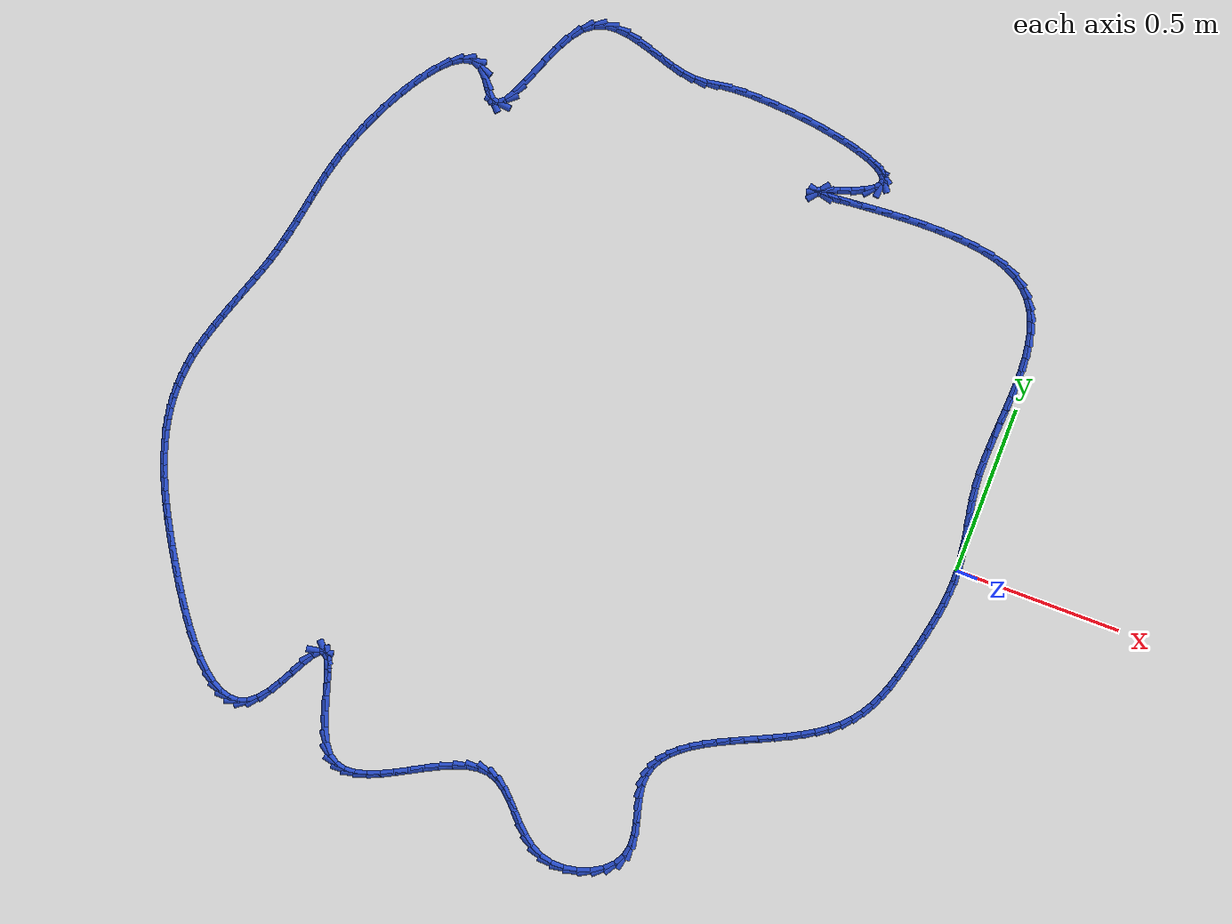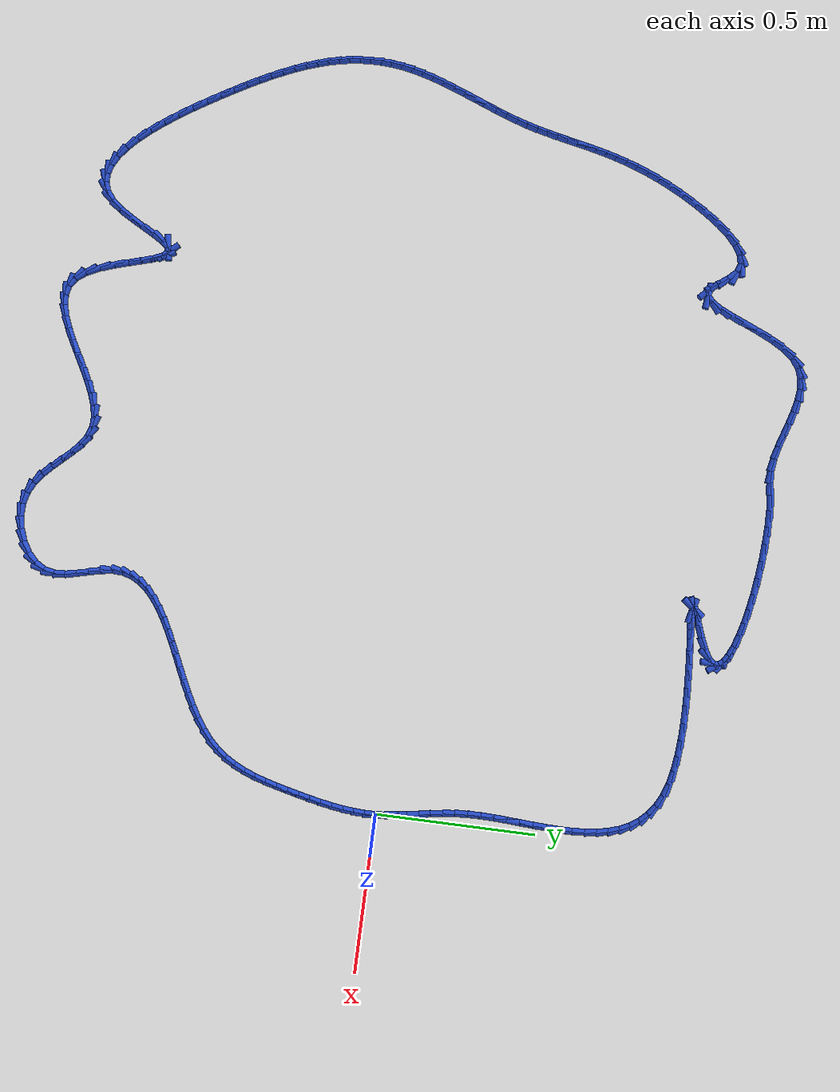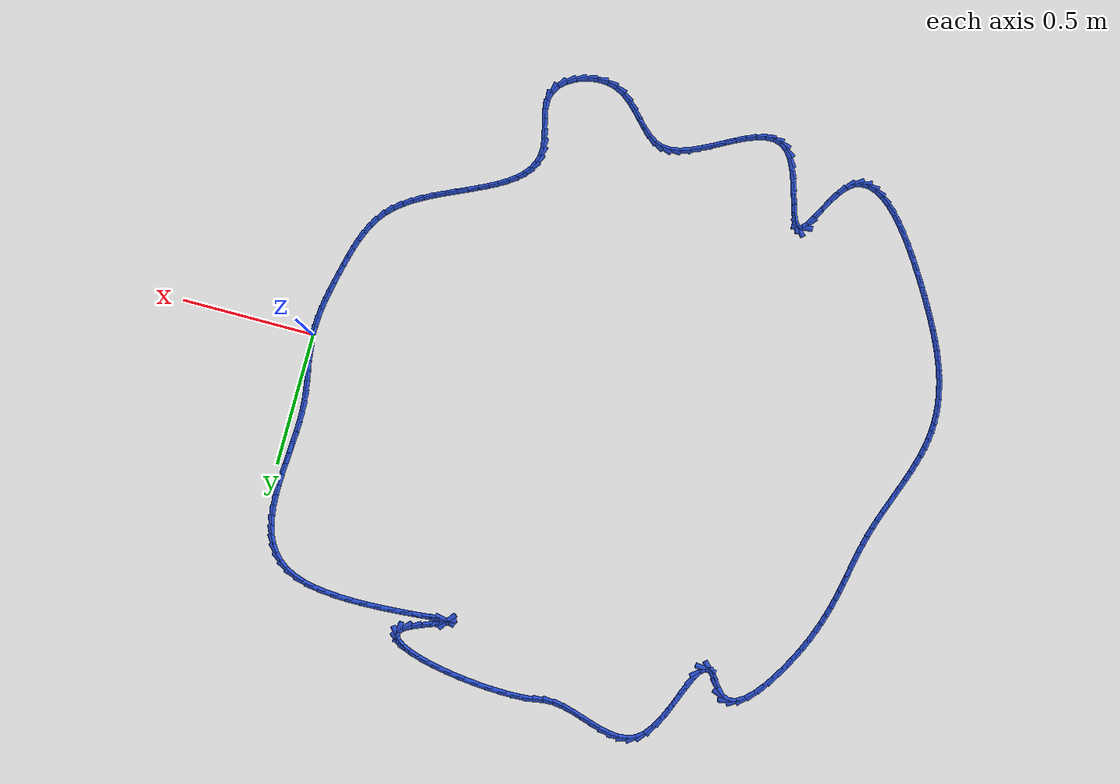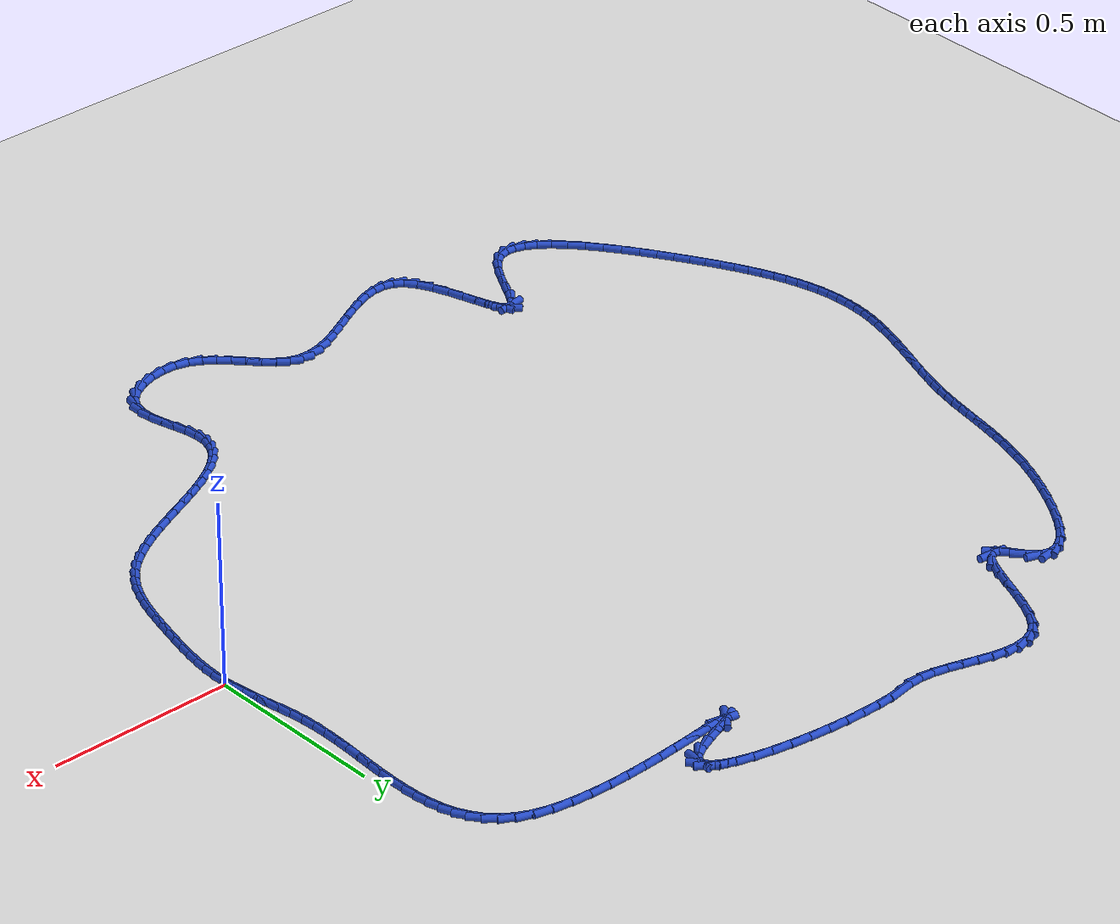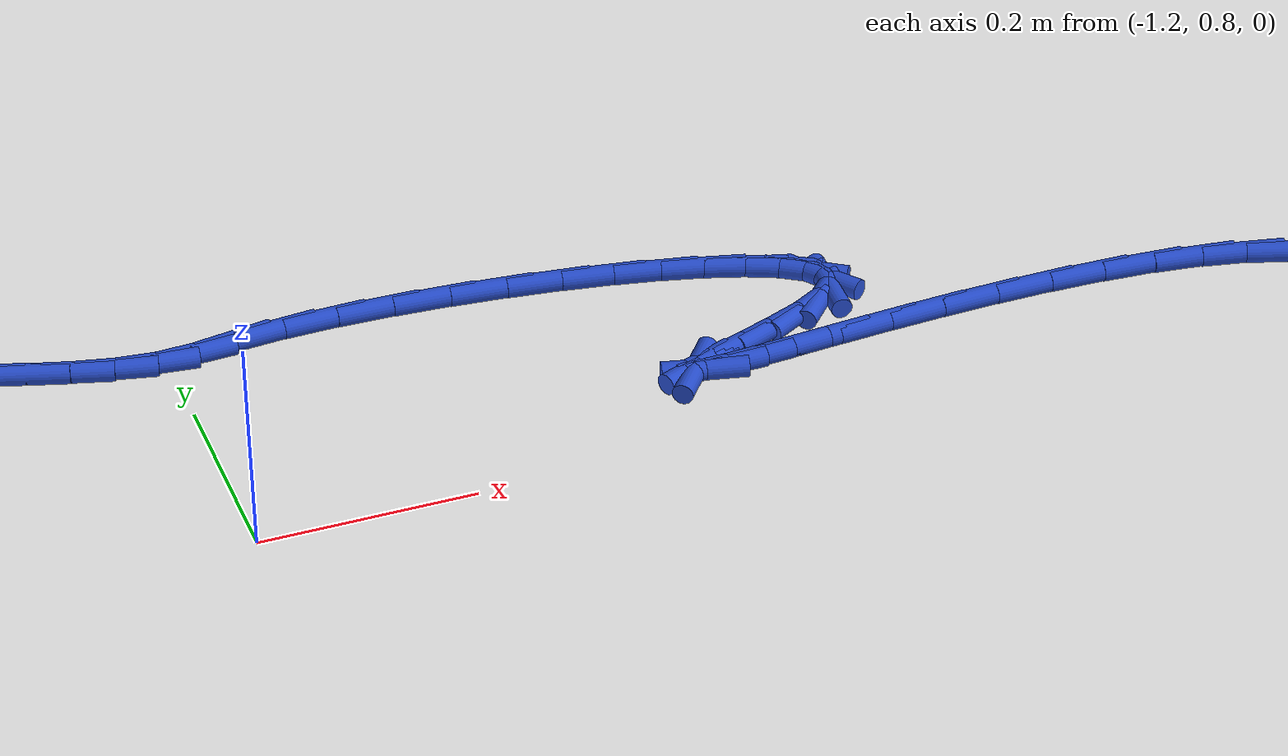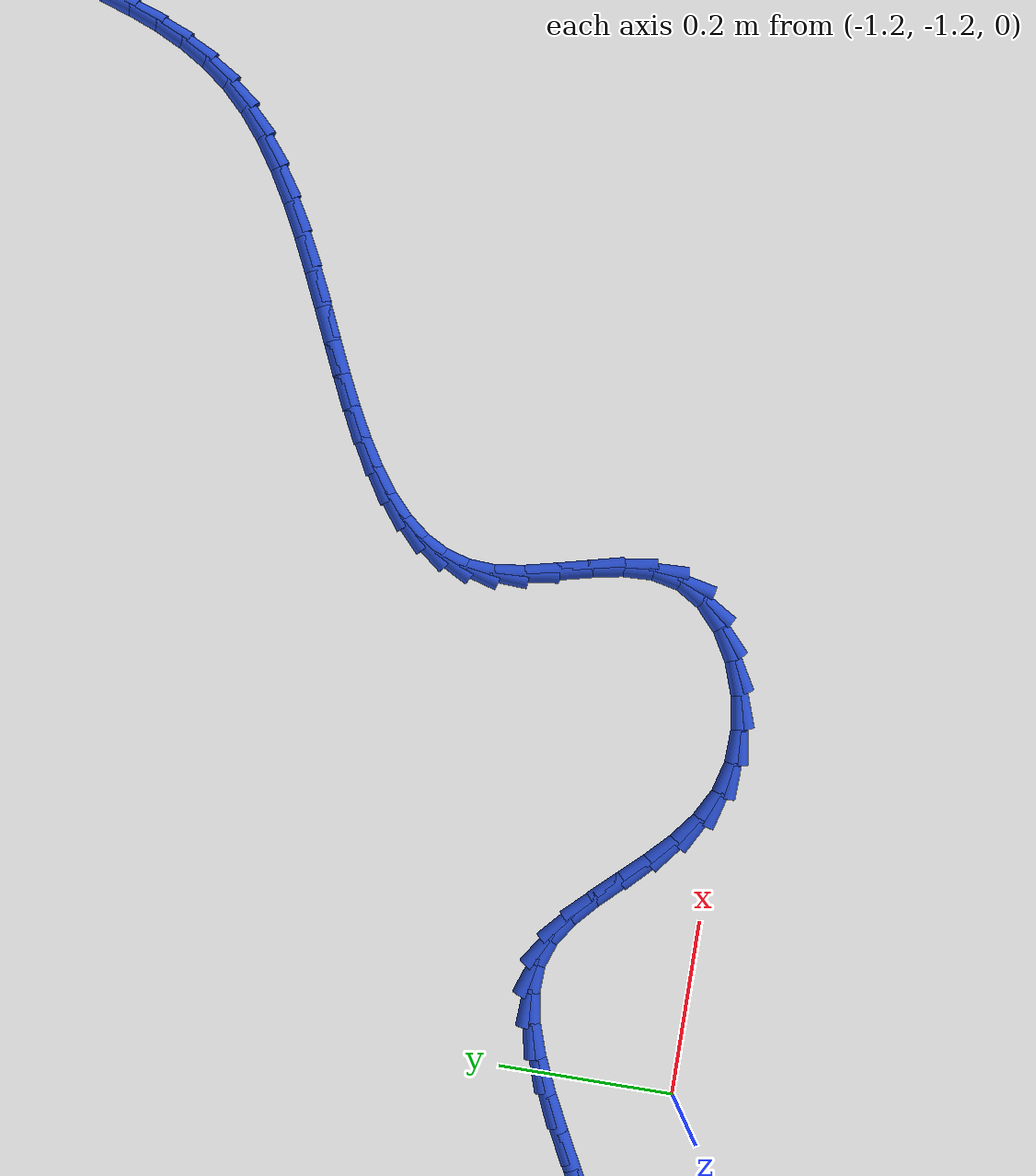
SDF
<sdf version="1.6">
 <world name="default">
  <light name="sun" type="directional">
   <pose>0 0 10 0 -0 0</pose>
   <diffuse>0.8 0.8 0.8 1</diffuse>
   <specular>0.2 0.2 0.2 1</specular>
   <attenuation>
    <range>1000</range>
    <constant>0.9</constant>
    <linear>0.01</linear>
    <quadratic>0.001</quadratic>
   </attenuation>
   <direction>-0.5 0.1 -0.9</direction>
  </light>
  <model name="ground_plane">
   <static>1</static>
   <link name="link">
    <collision name="collision">
     <geometry><plane><normal>0 0 1</normal><size>100 100</size></plane></geometry>
     <surface><friction><ode><mu>100</mu><mu2>50</mu2></ode></friction></surface>
    </collision>
    <visual name="visual">
     <cast_shadows>0</cast_shadows>
     <geometry><plane><normal>0 0 1</normal><size>100 100</size></plane></geometry>
     <material>
      <script><uri>file://media/materials/scripts/gazebo.material</uri><name>Gazebo/WhiteGlow</name></script>
     </material>
    </visual>
   </link>
  </model>
  <gravity>0 0 -9.8</gravity>
  <magnetic_field>6e-06 2.3e-05 -4.2e-05</magnetic_field>
  <atmosphere type="adiabatic"/>
  <physics name="default_physics" default="0" type="ode">
   <max_step_size>0.001</max_step_size>
   <real_time_factor>1</real_time_factor>
   <real_time_update_rate>1000</real_time_update_rate>
  </physics>
  <scene><ambient>0.4 0.4 0.4 1</ambient><background>0.7 0.7 0.7 1</background><shadows>1</shadows></scene>
  <spherical_coordinates>
   <surface_model>EARTH_WGS84</surface_model>
   <latitude_deg>0</latitude_deg>
   <longitude_deg>0</longitude_deg>
   <elevation>0</elevation>
   <heading_deg>0</heading_deg>
  </spherical_coordinates>
  <model name="line">
   <link name="link_0">
    <pose>-3.469446951953614e-18 3.469446951953614e-17 0.01 0 1.57 -1.4946058032906044</pose>
    <collision name="collision">
     <geometry><cylinder><radius>0.01</radius><length>0.08</length></cylinder></geometry>
    </collision>
    <visual name="visual">
     <material>
      <script><name>Gazebo/Blue</name><uri>file://media/materials/scripts/gazebo.material</uri></script>
     </material>
     <geometry><cylinder><radius>0.01</radius><length>0.08</length></cylinder></geometry>
    </visual>
   </link>
   <link name="link_1">
    <pose>-0.0026124231290593435 0.034221659290385974 0.01 0 1.57 -1.4421469915469958</pose>
    <collision name="collision">
     <geometry><cylinder><radius>0.01</radius><length>0.08</length></cylinder></geometry>
    </collision>
    <visual name="visual">
     <material>
      <script><name>Gazebo/Blue</name><uri>file://media/materials/scripts/gazebo.material</uri></script>
     </material>
     <geometry><cylinder><radius>0.01</radius><length>0.08</length></cylinder></geometry>
    </visual>
   </link>
   <link name="link_2">
    <pose>-0.007023234924951189 0.06831783988330072 0.01 0 1.57 -1.4082024537275601</pose>
    <collision name="collision">
     <geometry><cylinder><radius>0.01</radius><length>0.08</length></cylinder></geometry>
    </collision>
    <visual name="visual">
     <material>
      <script><name>Gazebo/Blue</name><uri>file://media/materials/scripts/gazebo.material</uri></script>
     </material>
     <geometry><cylinder><radius>0.01</radius><length>0.08</length></cylinder></geometry>
    </visual>
   </link>
   <link name="link_3">
    <pose>-0.012634603180972658 0.1025247381335995 0.01 0 1.57 -1.392860196229387</pose>
    <collision name="collision">
     <geometry><cylinder><radius>0.01</radius><length>0.08</length></cylinder></geometry>
    </collision>
    <visual name="visual">
     <material>
      <script><name>Gazebo/Blue</name><uri>file://media/materials/scripts/gazebo.material</uri></script>
     </material>
     <geometry><cylinder><radius>0.01</radius><length>0.08</length></cylinder></geometry>
    </visual>
   </link>
   <link name="link_4">
    <pose>-0.018848695690420848 0.13707855039613773 0.01 0 1.57 -1.395617671099398</pose>
    <collision name="collision">
     <geometry><cylinder><radius>0.01</radius><length>0.08</length></cylinder></geometry>
    </collision>
    <visual name="visual">
     <material>
      <script><name>Gazebo/Blue</name><uri>file://media/materials/scripts/gazebo.material</uri></script>
     </material>
     <geometry><cylinder><radius>0.01</radius><length>0.08</length></cylinder></geometry>
    </visual>
   </link>
   <link name="link_5">
    <pose>-0.025067680246592876 0.17221547302577064 0.01 0 1.57 -1.4155855629912089</pose>
    <collision name="collision">
     <geometry><cylinder><radius>0.01</radius><length>0.08</length></cylinder></geometry>
    </collision>
    <visual name="visual">
     <material>
      <script><name>Gazebo/Blue</name><uri>file://media/materials/scripts/gazebo.material</uri></script>
     </material>
     <geometry><cylinder><radius>0.01</radius><length>0.08</length></cylinder></geometry>
    </visual>
   </link>
   <link name="link_6">
    <pose>-0.03069372464278583 0.20817170237735358 0.01 0 1.57 -1.451530832151726</pose>
    <collision name="collision">
     <geometry><cylinder><radius>0.01</radius><length>0.08</length></cylinder></geometry>
    </collision>
    <visual name="visual">
     <material>
      <script><name>Gazebo/Blue</name><uri>file://media/materials/scripts/gazebo.material</uri></script>
     </material>
     <geometry><cylinder><radius>0.01</radius><length>0.08</length></cylinder></geometry>
    </visual>
   </link>
   <link name="link_7">
    <pose>-0.03512899667229684 0.2451834348057419 0.01 0 1.57 -1.5015947000845757</pose>
    <collision name="collision">
     <geometry><cylinder><radius>0.01</radius><length>0.08</length></cylinder></geometry>
    </collision>
    <visual name="visual">
     <material>
      <script><name>Gazebo/Blue</name><uri>file://media/materials/scripts/gazebo.material</uri></script>
     </material>
     <geometry><cylinder><radius>0.01</radius><length>0.08</length></cylinder></geometry>
    </visual>
   </link>
   <link name="link_8">
    <pose>-0.03778361329504823 0.2834827907832505 0.01 0 1.57 -1.5531393959789488</pose>
    <collision name="collision">
     <geometry><cylinder><radius>0.01</radius><length>0.08</length></cylinder></geometry>
    </collision>
    <visual name="visual">
     <material>
      <script><name>Gazebo/Blue</name><uri>file://media/materials/scripts/gazebo.material</uri></script>
     </material>
     <geometry><cylinder><radius>0.01</radius><length>0.08</length></cylinder></geometry>
    </visual>
   </link>
   <link name="link_9">
    <pose>-0.038483009006625886 0.32308893946640915 0.01 0 1.57 1.5506167041044434</pose>
    <collision name="collision">
     <geometry><cylinder><radius>0.01</radius><length>0.08</length></cylinder></geometry>
    </collision>
    <visual name="visual">
     <material>
      <script><name>Gazebo/Blue</name><uri>file://media/materials/scripts/gazebo.material</uri></script>
     </material>
     <geometry><cylinder><radius>0.01</radius><length>0.08</length></cylinder></geometry>
    </visual>
   </link>
   <link name="link_10">
    <pose>-0.037663221066826215 0.36370796748838785 0.01 0 1.57 1.5259470286337846</pose>
    <collision name="collision">
     <geometry><cylinder><radius>0.01</radius><length>0.08</length></cylinder></geometry>
    </collision>
    <visual name="visual">
     <material>
      <script><name>Gazebo/Blue</name><uri>file://media/materials/scripts/gazebo.material</uri></script>
     </material>
     <geometry><cylinder><radius>0.01</radius><length>0.08</length></cylinder></geometry>
    </visual>
   </link>
   <link name="link_11">
    <pose>-0.03580912072811332 0.4050209221760414 0.01 0 1.57 1.5132045105530816</pose>
    <collision name="collision">
     <geometry><cylinder><radius>0.01</radius><length>0.08</length></cylinder></geometry>
    </collision>
    <visual name="visual">
     <material>
      <script><name>Gazebo/Blue</name><uri>file://media/materials/scripts/gazebo.material</uri></script>
     </material>
     <geometry><cylinder><radius>0.01</radius><length>0.08</length></cylinder></geometry>
    </visual>
   </link>
   <link name="link_12">
    <pose>-0.03340557924295126 0.446708850856224 0.01 0 1.57 1.5117400703557264</pose>
    <collision name="collision">
     <geometry><cylinder><radius>0.01</radius><length>0.08</length></cylinder></geometry>
    </collision>
    <visual name="visual">
     <material>
      <script><name>Gazebo/Blue</name><uri>file://media/materials/scripts/gazebo.material</uri></script>
     </material>
     <geometry><cylinder><radius>0.01</radius><length>0.08</length></cylinder></geometry>
    </visual>
   </link>
   <link name="link_13">
    <pose>-0.030937467863804132 0.4884528008557906 0.01 0 1.57 1.5214689738055565</pose>
    <collision name="collision">
     <geometry><cylinder><radius>0.01</radius><length>0.08</length></cylinder></geometry>
    </collision>
    <visual name="visual">
     <material>
      <script><name>Gazebo/Blue</name><uri>file://media/materials/scripts/gazebo.material</uri></script>
     </material>
     <geometry><cylinder><radius>0.01</radius><length>0.08</length></cylinder></geometry>
    </visual>
   </link>
   <link name="link_14">
    <pose>-0.028889657843136015 0.5299338195015956 0.01 0 1.57 1.5428656560708973</pose>
    <collision name="collision">
     <geometry><cylinder><radius>0.01</radius><length>0.08</length></cylinder></geometry>
    </collision>
    <visual name="visual">
     <material>
      <script><name>Gazebo/Blue</name><uri>file://media/materials/scripts/gazebo.material</uri></script>
     </material>
     <geometry><cylinder><radius>0.01</radius><length>0.08</length></cylinder></geometry>
    </visual>
   </link>
   <link name="link_15">
    <pose>-0.02774702043341098 0.5708329541204941 0.01 0 1.57 -1.5646109811323707</pose>
    <collision name="collision">
     <geometry><cylinder><radius>0.01</radius><length>0.08</length></cylinder></geometry>
    </collision>
    <visual name="visual">
     <material>
      <script><name>Gazebo/Blue</name><uri>file://media/materials/scripts/gazebo.material</uri></script>
     </material>
     <geometry><cylinder><radius>0.01</radius><length>0.08</length></cylinder></geometry>
    </visual>
   </link>
   <link name="link_16">
    <pose>-0.02799442688709313 0.6108312520393402 0.01 0 1.57 -1.5161215480757144</pose>
    <collision name="collision">
     <geometry><cylinder><radius>0.01</radius><length>0.08</length></cylinder></geometry>
    </collision>
    <visual name="visual">
     <material>
      <script><name>Gazebo/Blue</name><uri>file://media/materials/scripts/gazebo.material</uri></script>
     </material>
     <geometry><cylinder><radius>0.01</radius><length>0.08</length></cylinder></geometry>
    </visual>
   </link>
   <link name="link_17">
    <pose>-0.03011674845664654 0.6496097605849891 0.01 0 1.57 -1.4510143886595541</pose>
    <collision name="collision">
     <geometry><cylinder><radius>0.01</radius><length>0.08</length></cylinder></geometry>
    </collision>
    <visual name="visual">
     <material>
      <script><name>Gazebo/Blue</name><uri>file://media/materials/scripts/gazebo.material</uri></script>
     </material>
     <geometry><cylinder><radius>0.01</radius><length>0.08</length></cylinder></geometry>
    </visual>
   </link>
   <link name="link_18">
    <pose>-0.03459885639453528 0.6868495270842949 0.01 0 1.57 -1.3666066055802346</pose>
    <collision name="collision">
     <geometry><cylinder><radius>0.01</radius><length>0.08</length></cylinder></geometry>
    </collision>
    <visual name="visual">
     <material>
      <script><name>Gazebo/Blue</name><uri>file://media/materials/scripts/gazebo.material</uri></script>
     </material>
     <geometry><cylinder><radius>0.01</radius><length>0.08</length></cylinder></geometry>
    </visual>
   </link>
   <link name="link_19">
    <pose>-0.04192562195322343 0.7222315988641121 0.01 0 1.57 -1.260258799297225</pose>
    <collision name="collision">
     <geometry><cylinder><radius>0.01</radius><length>0.08</length></cylinder></geometry>
    </collision>
    <visual name="visual">
     <material>
      <script><name>Gazebo/Blue</name><uri>file://media/materials/scripts/gazebo.material</uri></script>
     </material>
     <geometry><cylinder><radius>0.01</radius><length>0.08</length></cylinder></geometry>
    </visual>
   </link>
   <link name="link_20">
    <pose>-0.0525819163851751 0.7554370232512961 0.01 0 1.57 -1.1304470077338153</pose>
    <collision name="collision">
     <geometry><cylinder><radius>0.01</radius><length>0.08</length></cylinder></geometry>
    </collision>
    <visual name="visual">
     <material>
      <script><name>Gazebo/Blue</name><uri>file://media/materials/scripts/gazebo.material</uri></script>
     </material>
     <geometry><cylinder><radius>0.01</radius><length>0.08</length></cylinder></geometry>
    </visual>
   </link>
   <link name="link_21">
    <pose>-0.06705261094285433 0.786146847572701 0.01 0 1.57 -0.9785095552409157</pose>
    <collision name="collision">
     <geometry><cylinder><radius>0.01</radius><length>0.08</length></cylinder></geometry>
    </collision>
    <visual name="visual">
     <material>
      <script><name>Gazebo/Blue</name><uri>file://media/materials/scripts/gazebo.material</uri></script>
     </material>
     <geometry><cylinder><radius>0.01</radius><length>0.08</length></cylinder></geometry>
    </visual>
   </link>
   <link name="link_22">
    <pose>-0.08582257687872528 0.8140421191551817 0.01 0 1.57 -0.810388008019312</pose>
    <collision name="collision">
     <geometry><cylinder><radius>0.01</radius><length>0.08</length></cylinder></geometry>
    </collision>
    <visual name="visual">
     <material>
      <script><name>Gazebo/Blue</name><uri>file://media/materials/scripts/gazebo.material</uri></script>
     </material>
     <geometry><cylinder><radius>0.01</radius><length>0.08</length></cylinder></geometry>
    </visual>
   </link>
   <link name="link_23">
    <pose>-0.10937668544525198 0.8388038853255926 0.01 0 1.57 -0.6366262468930142</pose>
    <collision name="collision">
     <geometry><cylinder><radius>0.01</radius><length>0.08</length></cylinder></geometry>
    </collision>
    <visual name="visual">
     <material>
      <script><name>Gazebo/Blue</name><uri>file://media/materials/scripts/gazebo.material</uri></script>
     </material>
     <geometry><cylinder><radius>0.01</radius><length>0.08</length></cylinder></geometry>
    </visual>
   </link>
   <link name="link_24">
    <pose>-0.1381998078948985 0.8601131934107883 0.01 0 1.57 -0.4694011049189898</pose>
    <collision name="collision">
     <geometry><cylinder><radius>0.01</radius><length>0.08</length></cylinder></geometry>
    </collision>
    <visual name="visual">
     <material>
      <script><name>Gazebo/Blue</name><uri>file://media/materials/scripts/gazebo.material</uri></script>
     </material>
     <geometry><cylinder><radius>0.01</radius><length>0.08</length></cylinder></geometry>
    </visual>
   </link>
   <link name="link_25">
    <pose>-0.1727768154801288 0.8776510907376236 0.01 0 1.57 -0.3194768551653633</pose>
    <collision name="collision">
     <geometry><cylinder><radius>0.01</radius><length>0.08</length></cylinder></geometry>
    </collision>
    <visual name="visual">
     <material>
      <script><name>Gazebo/Blue</name><uri>file://media/materials/scripts/gazebo.material</uri></script>
     </material>
     <geometry><cylinder><radius>0.01</radius><length>0.08</length></cylinder></geometry>
    </visual>
   </link>
   <link name="link_26">
    <pose>-0.2135224040643267 0.8911300944748518 0.01 0 1.57 -0.20392701906793143</pose>
    <collision name="collision">
     <geometry><cylinder><radius>0.01</radius><length>0.08</length></cylinder></geometry>
    </collision>
    <visual name="visual">
     <material>
      <script><name>Gazebo/Blue</name><uri>file://media/materials/scripts/gazebo.material</uri></script>
     </material>
     <geometry><cylinder><radius>0.01</radius><length>0.08</length></cylinder></geometry>
    </visual>
   </link>
   <link name="link_27">
    <pose>-0.259851551508749 0.9007110408940092 0.01 0 1.57 -0.1215271285258354</pose>
    <collision name="collision">
     <geometry><cylinder><radius>0.01</radius><length>0.08</length></cylinder></geometry>
    </collision>
    <visual name="visual">
     <material>
      <script><name>Gazebo/Blue</name><uri>file://media/materials/scripts/gazebo.material</uri></script>
     </material>
     <geometry><cylinder><radius>0.01</radius><length>0.08</length></cylinder></geometry>
    </visual>
   </link>
   <link name="link_28">
    <pose>-0.3104345983256323 0.9068886955822022 0.01 0 1.57 -0.06118965568954185</pose>
    <collision name="collision">
     <geometry><cylinder><radius>0.01</radius><length>0.08</length></cylinder></geometry>
    </collision>
    <visual name="visual">
     <material>
      <script><name>Gazebo/Blue</name><uri>file://media/materials/scripts/gazebo.material</uri></script>
     </material>
     <geometry><cylinder><radius>0.01</radius><length>0.08</length></cylinder></geometry>
    </visual>
   </link>
   <link name="link_29">
    <pose>-0.36392411754773313 0.9101657918738825 0.01 0 1.57 -0.01597128774711251</pose>
    <collision name="collision">
     <geometry><cylinder><radius>0.01</radius><length>0.08</length></cylinder></geometry>
    </collision>
    <visual name="visual">
     <material>
      <script><name>Gazebo/Blue</name><uri>file://media/materials/scripts/gazebo.material</uri></script>
     </material>
     <geometry><cylinder><radius>0.01</radius><length>0.08</length></cylinder></geometry>
    </visual>
   </link>
   <link name="link_30">
    <pose>-0.4189726822078089 0.9110450631035029 0.01 0 1.57 0.018380433122437503</pose>
    <collision name="collision">
     <geometry><cylinder><radius>0.01</radius><length>0.08</length></cylinder></geometry>
    </collision>
    <visual name="visual">
     <material>
      <script><name>Gazebo/Blue</name><uri>file://media/materials/scripts/gazebo.material</uri></script>
     </material>
     <geometry><cylinder><radius>0.01</radius><length>0.08</length></cylinder></geometry>
    </visual>
   </link>
   <link name="link_31">
    <pose>-0.4742328653386162 0.9100292426055155 0.01 0 1.57 0.04446410075200229</pose>
    <collision name="collision">
     <geometry><cylinder><radius>0.01</radius><length>0.08</length></cylinder></geometry>
    </collision>
    <visual name="visual">
     <material>
      <script><name>Gazebo/Blue</name><uri>file://media/materials/scripts/gazebo.material</uri></script>
     </material>
     <geometry><cylinder><radius>0.01</radius><length>0.08</length></cylinder></geometry>
    </visual>
   </link>
   <link name="link_32">
    <pose>-0.5283572399729122 0.9076210637143733 0.01 0 1.57 0.06377341812137298</pose>
    <collision name="collision">
     <geometry><cylinder><radius>0.01</radius><length>0.08</length></cylinder></geometry>
    </collision>
    <visual name="visual">
     <material>
      <script><name>Gazebo/Blue</name><uri>file://media/materials/scripts/gazebo.material</uri></script>
     </material>
     <geometry><cylinder><radius>0.01</radius><length>0.08</length></cylinder></geometry>
    </visual>
   </link>
   <link name="link_33">
    <pose>-0.5799983791434535 0.9043232597645285 0.01 0 1.57 0.07691674731030786</pose>
    <collision name="collision">
     <geometry><cylinder><radius>0.01</radius><length>0.08</length></cylinder></geometry>
    </collision>
    <visual name="visual">
     <material>
      <script><name>Gazebo/Blue</name><uri>file://media/materials/scripts/gazebo.material</uri></script>
     </material>
     <geometry><cylinder><radius>0.01</radius><length>0.08</length></cylinder></geometry>
    </visual>
   </link>
   <link name="link_34">
    <pose>-0.6278088558829971 0.9006385640904335 0.01 0 1.57 0.08351754673476734</pose>
    <collision name="collision">
     <geometry><cylinder><radius>0.01</radius><length>0.08</length></cylinder></geometry>
    </collision>
    <visual name="visual">
     <material>
      <script><name>Gazebo/Blue</name><uri>file://media/materials/scripts/gazebo.material</uri></script>
     </material>
     <geometry><cylinder><radius>0.01</radius><length>0.08</length></cylinder></geometry>
    </visual>
   </link>
   <link name="link_35">
    <pose>-0.6704412432242999 0.8970697100265408 0.01 0 1.57 0.08152851260966233</pose>
    <collision name="collision">
     <geometry><cylinder><radius>0.01</radius><length>0.08</length></cylinder></geometry>
    </collision>
    <visual name="visual">
     <material>
      <script><name>Gazebo/Blue</name><uri>file://media/materials/scripts/gazebo.material</uri></script>
     </material>
     <geometry><cylinder><radius>0.01</radius><length>0.08</length></cylinder></geometry>
    </visual>
   </link>
   <link name="link_36">
    <pose>-0.706548114200119 0.8941194309073028 0.01 0 1.57 0.06468880120953734</pose>
    <collision name="collision">
     <geometry><cylinder><radius>0.01</radius><length>0.08</length></cylinder></geometry>
    </collision>
    <visual name="visual">
     <material>
      <script><name>Gazebo/Blue</name><uri>file://media/materials/scripts/gazebo.material</uri></script>
     </material>
     <geometry><cylinder><radius>0.01</radius><length>0.08</length></cylinder></geometry>
    </visual>
   </link>
   <link name="link_37">
    <pose>-0.7347820418432112 0.8922904600671718 0.01 0 1.57 0.010777640823340822</pose>
    <collision name="collision">
     <geometry><cylinder><radius>0.01</radius><length>0.08</length></cylinder></geometry>
    </collision>
    <visual name="visual">
     <material>
      <script><name>Gazebo/Blue</name><uri>file://media/materials/scripts/gazebo.material</uri></script>
     </material>
     <geometry><cylinder><radius>0.01</radius><length>0.08</length></cylinder></geometry>
    </visual>
   </link>
   <link name="link_38">
    <pose>-0.7537955991863332 0.8920855308406005 0.01 0 1.57 -0.22374170483796854</pose>
    <collision name="collision">
     <geometry><cylinder><radius>0.01</radius><length>0.08</length></cylinder></geometry>
    </collision>
    <visual name="visual">
     <material>
      <script><name>Gazebo/Blue</name><uri>file://media/materials/scripts/gazebo.material</uri></script>
     </material>
     <geometry><cylinder><radius>0.01</radius><length>0.08</length></cylinder></geometry>
    </visual>
   </link>
   <link name="link_39">
    <pose>-0.7622413592622418 0.8940073765620411 0.01 0 1.57 0.9194741668668903</pose>
    <collision name="collision">
     <geometry><cylinder><radius>0.01</radius><length>0.08</length></cylinder></geometry>
    </collision>
    <visual name="visual">
     <material>
      <script><name>Gazebo/Blue</name><uri>file://media/materials/scripts/gazebo.material</uri></script>
     </material>
     <geometry><cylinder><radius>0.01</radius><length>0.08</length></cylinder></geometry>
    </visual>
   </link>
   <link name="link_40">
    <pose>-0.7587718951036945 0.8985587305659463 0.01 0 1.57 0.43048878484852804</pose>
    <collision name="collision">
     <geometry><cylinder><radius>0.01</radius><length>0.08</length></cylinder></geometry>
    </collision>
    <visual name="visual">
     <material>
      <script><name>Gazebo/Blue</name><uri>file://media/materials/scripts/gazebo.material</uri></script>
     </material>
     <geometry><cylinder><radius>0.01</radius><length>0.08</length></cylinder></geometry>
    </visual>
   </link>
   <link name="link_41">
    <pose>-0.7420397971591669 0.9062423232550538 0.01 0 1.57 0.3556529765919658</pose>
    <collision name="collision">
     <geometry><cylinder><radius>0.01</radius><length>0.08</length></cylinder></geometry>
    </collision>
    <visual name="visual">
     <material>
      <script><name>Gazebo/Blue</name><uri>file://media/materials/scripts/gazebo.material</uri></script>
     </material>
     <geometry><cylinder><radius>0.01</radius><length>0.08</length></cylinder></geometry>
    </visual>
   </link>
   <link name="link_42">
    <pose>-0.7122899624817576 0.9172928404972882 0.01 0 1.57 0.3572307348656074</pose>
    <collision name="collision">
     <geometry><cylinder><radius>0.01</radius><length>0.08</length></cylinder></geometry>
    </collision>
    <visual name="visual">
     <material>
      <script><name>Gazebo/Blue</name><uri>file://media/materials/scripts/gazebo.material</uri></script>
     </material>
     <geometry><cylinder><radius>0.01</radius><length>0.08</length></cylinder></geometry>
    </visual>
   </link>
   <link name="link_43">
    <pose>-0.6757174319126646 0.9309433372440624 0.01 0 1.57 0.402582470246729</pose>
    <collision name="collision">
     <geometry><cylinder><radius>0.01</radius><length>0.08</length></cylinder></geometry>
    </collision>
    <visual name="visual">
     <material>
      <script><name>Gazebo/Blue</name><uri>file://media/materials/scripts/gazebo.material</uri></script>
     </material>
     <geometry><cylinder><radius>0.01</radius><length>0.08</length></cylinder></geometry>
    </visual>
   </link>
   <link name="link_44">
    <pose>-0.6399068203657324 0.9461929513514199 0.01 0 1.57 0.523259841015723</pose>
    <collision name="collision">
     <geometry><cylinder><radius>0.01</radius><length>0.08</length></cylinder></geometry>
    </collision>
    <visual name="visual">
     <material>
      <script><name>Gazebo/Blue</name><uri>file://media/materials/scripts/gazebo.material</uri></script>
     </material>
     <geometry><cylinder><radius>0.01</radius><length>0.08</length></cylinder></geometry>
    </visual>
   </link>
   <link name="link_45">
    <pose>-0.6124346836049726 0.9620415843243194 0.01 0 1.57 0.8435571485170217</pose>
    <collision name="collision">
     <geometry><cylinder><radius>0.01</radius><length>0.08</length></cylinder></geometry>
    </collision>
    <visual name="visual">
     <material>
      <script><name>Gazebo/Blue</name><uri>file://media/materials/scripts/gazebo.material</uri></script>
     </material>
     <geometry><cylinder><radius>0.01</radius><length>0.08</length></cylinder></geometry>
    </visual>
   </link>
   <link name="link_46">
    <pose>-0.5984852726740374 0.977715821740542 0.01 0 1.57 1.5078199339795337</pose>
    <collision name="collision">
     <geometry><cylinder><radius>0.01</radius><length>0.08</length></cylinder></geometry>
    </collision>
    <visual name="visual">
     <material>
      <script><name>Gazebo/Blue</name><uri>file://media/materials/scripts/gazebo.material</uri></script>
     </material>
     <geometry><cylinder><radius>0.01</radius><length>0.08</length></cylinder></geometry>
    </visual>
   </link>
   <link name="link_47">
    <pose>-0.5975224465508996 0.9929842878908055 0.01 0 1.57 -0.9441405588081778</pose>
    <collision name="collision">
     <geometry><cylinder><radius>0.01</radius><length>0.08</length></cylinder></geometry>
    </collision>
    <visual name="visual">
     <material>
      <script><name>Gazebo/Blue</name><uri>file://media/materials/scripts/gazebo.material</uri></script>
     </material>
     <geometry><cylinder><radius>0.01</radius><length>0.08</length></cylinder></geometry>
    </visual>
   </link>
   <link name="link_48">
    <pose>-0.6081730205876004 1.0076949215681312 0.01 0 1.57 -0.5904359452761297</pose>
    <collision name="collision">
     <geometry><cylinder><radius>0.01</radius><length>0.08</length></cylinder></geometry>
    </collision>
    <visual name="visual">
     <material>
      <script><name>Gazebo/Blue</name><uri>file://media/materials/scripts/gazebo.material</uri></script>
     </material>
     <geometry><cylinder><radius>0.01</radius><length>0.08</length></cylinder></geometry>
    </visual>
   </link>
   <link name="link_49">
    <pose>-0.6290638101361814 1.0216956615655417 0.01 0 1.57 -0.415782775708621</pose>
    <collision name="collision">
     <geometry><cylinder><radius>0.01</radius><length>0.08</length></cylinder></geometry>
    </collision>
    <visual name="visual">
     <material>
      <script><name>Gazebo/Blue</name><uri>file://media/materials/scripts/gazebo.material</uri></script>
     </material>
     <geometry><cylinder><radius>0.01</radius><length>0.08</length></cylinder></geometry>
    </visual>
   </link>
   <link name="link_50">
    <pose>-0.6588216305486843 1.0348344466760586 0.01 0 1.57 -0.314668325253031</pose>
    <collision name="collision">
     <geometry><cylinder><radius>0.01</radius><length>0.08</length></cylinder></geometry>
    </collision>
    <visual name="visual">
     <material>
      <script><name>Gazebo/Blue</name><uri>file://media/materials/scripts/gazebo.material</uri></script>
     </material>
     <geometry><cylinder><radius>0.01</radius><length>0.08</length></cylinder></geometry>
    </visual>
   </link>
   <link name="link_51">
    <pose>-0.6960732971771507 1.0469592156927043 0.01 0 1.57 -0.24748580707257362</pose>
    <collision name="collision">
     <geometry><cylinder><radius>0.01</radius><length>0.08</length></cylinder></geometry>
    </collision>
    <visual name="visual">
     <material>
      <script><name>Gazebo/Blue</name><uri>file://media/materials/scripts/gazebo.material</uri></script>
     </material>
     <geometry><cylinder><radius>0.01</radius><length>0.08</length></cylinder></geometry>
    </visual>
   </link>
   <link name="link_52">
    <pose>-0.7394456253736219 1.0579179074085003 0.01 0 1.57 -0.19772708582464</pose>
    <collision name="collision">
     <geometry><cylinder><radius>0.01</radius><length>0.08</length></cylinder></geometry>
    </collision>
    <visual name="visual">
     <material>
      <script><name>Gazebo/Blue</name><uri>file://media/materials/scripts/gazebo.material</uri></script>
     </material>
     <geometry><cylinder><radius>0.01</radius><length>0.08</length></cylinder></geometry>
    </visual>
   </link>
   <link name="link_53">
    <pose>-0.7875654304901394 1.067558460616468 0.01 0 1.57 -0.15735412035748672</pose>
    <collision name="collision">
     <geometry><cylinder><radius>0.01</radius><length>0.08</length></cylinder></geometry>
    </collision>
    <visual name="visual">
     <material>
      <script><name>Gazebo/Blue</name><uri>file://media/materials/scripts/gazebo.material</uri></script>
     </material>
     <geometry><cylinder><radius>0.01</radius><length>0.08</length></cylinder></geometry>
    </visual>
   </link>
   <link name="link_54">
    <pose>-0.8390595278787453 1.0757288141096304 0.01 0 1.57 -0.1217993279170763</pose>
    <collision name="collision">
     <geometry><cylinder><radius>0.01</radius><length>0.08</length></cylinder></geometry>
    </collision>
    <visual name="visual">
     <material>
      <script><name>Gazebo/Blue</name><uri>file://media/materials/scripts/gazebo.material</uri></script>
     </material>
     <geometry><cylinder><radius>0.01</radius><length>0.08</length></cylinder></geometry>
    </visual>
   </link>
   <link name="link_55">
    <pose>-0.8925547328914805 1.0822769066810087 0.01 0 1.57 -0.08797437883109932</pose>
    <collision name="collision">
     <geometry><cylinder><radius>0.01</radius><length>0.08</length></cylinder></geometry>
    </collision>
    <visual name="visual">
     <material>
      <script><name>Gazebo/Blue</name><uri>file://media/materials/scripts/gazebo.material</uri></script>
     </material>
     <geometry><cylinder><radius>0.01</radius><length>0.08</length></cylinder></geometry>
    </visual>
   </link>
   <link name="link_56">
    <pose>-0.9466778608803869 1.0870506771236246 0.01 0 1.57 -0.05329345445261039</pose>
    <collision name="collision">
     <geometry><cylinder><radius>0.01</radius><length>0.08</length></cylinder></geometry>
    </collision>
    <visual name="visual">
     <material>
      <script><name>Gazebo/Blue</name><uri>file://media/materials/scripts/gazebo.material</uri></script>
     </material>
     <geometry><cylinder><radius>0.01</radius><length>0.08</length></cylinder></geometry>
    </visual>
   </link>
   <link name="link_57">
    <pose>-1.0000557271975055 1.0898980642305005 0.01 0 1.57 -0.014999875020055994</pose>
    <collision name="collision">
     <geometry><cylinder><radius>0.01</radius><length>0.08</length></cylinder></geometry>
    </collision>
    <visual name="visual">
     <material>
      <script><name>Gazebo/Blue</name><uri>file://media/materials/scripts/gazebo.material</uri></script>
     </material>
     <geometry><cylinder><radius>0.01</radius><length>0.08</length></cylinder></geometry>
    </visual>
   </link>
   <link name="link_58">
    <pose>-1.0513151471948783 1.090667006794658 0.01 0 1.57 0.030587711301038586</pose>
    <collision name="collision">
     <geometry><cylinder><radius>0.01</radius><length>0.08</length></cylinder></geometry>
    </collision>
    <visual name="visual">
     <material>
      <script><name>Gazebo/Blue</name><uri>file://media/materials/scripts/gazebo.material</uri></script>
     </material>
     <geometry><cylinder><radius>0.01</radius><length>0.08</length></cylinder></geometry>
    </visual>
   </link>
   <link name="link_59">
    <pose>-1.0990829362245473 1.0892054436091194 0.01 0 1.57 0.08936192257964314</pose>
    <collision name="collision">
     <geometry><cylinder><radius>0.01</radius><length>0.08</length></cylinder></geometry>
    </collision>
    <visual name="visual">
     <material>
      <script><name>Gazebo/Blue</name><uri>file://media/materials/scripts/gazebo.material</uri></script>
     </material>
     <geometry><cylinder><radius>0.01</radius><length>0.08</length></cylinder></geometry>
    </visual>
   </link>
   <link name="link_60">
    <pose>-1.141985909638553 1.0853613134669065 0.01 0 1.57 0.16446638013485715</pose>
    <collision name="collision">
     <geometry><cylinder><radius>0.01</radius><length>0.08</length></cylinder></geometry>
    </collision>
    <visual name="visual">
     <material>
      <script><name>Gazebo/Blue</name><uri>file://media/materials/scripts/gazebo.material</uri></script>
     </material>
     <geometry><cylinder><radius>0.01</radius><length>0.08</length></cylinder></geometry>
    </visual>
   </link>
   <link name="link_61">
    <pose>-1.1788720965606032 1.0792394791473934 0.01 0 1.57 0.04945068046576197</pose>
    <collision name="collision">
     <geometry><cylinder><radius>0.01</radius><length>0.08</length></cylinder></geometry>
    </collision>
    <visual name="visual">
     <material>
      <script><name>Gazebo/Blue</name><uri>file://media/materials/scripts/gazebo.material</uri></script>
     </material>
     <geometry><cylinder><radius>0.01</radius><length>0.08</length></cylinder></geometry>
    </visual>
   </link>
   <link name="link_62">
    <pose>-1.2147236766185288 1.0774651475829788 0.01 0 1.57 -0.1163055687142159</pose>
    <collision name="collision">
     <geometry><cylinder><radius>0.01</radius><length>0.08</length></cylinder></geometry>
    </collision>
    <visual name="visual">
     <material>
      <script><name>Gazebo/Blue</name><uri>file://media/materials/scripts/gazebo.material</uri></script>
     </material>
     <geometry><cylinder><radius>0.01</radius><length>0.08</length></cylinder></geometry>
    </visual>
   </link>
   <link name="link_63">
    <pose>-1.2518745875602613 1.0818055941324756 0.01 0 1.57 -0.22411433266845757</pose>
    <collision name="collision">
     <geometry><cylinder><radius>0.01</radius><length>0.08</length></cylinder></geometry>
    </collision>
    <visual name="visual">
     <material>
      <script><name>Gazebo/Blue</name><uri>file://media/materials/scripts/gazebo.material</uri></script>
     </material>
     <geometry><cylinder><radius>0.01</radius><length>0.08</length></cylinder></geometry>
    </visual>
   </link>
   <link name="link_64">
    <pose>-1.2898695579406814 1.0904663005414297 0.01 0 1.57 -0.28358245034540364</pose>
    <collision name="collision">
     <geometry><cylinder><radius>0.01</radius><length>0.08</length></cylinder></geometry>
    </collision>
    <visual name="visual">
     <material>
      <script><name>Gazebo/Blue</name><uri>file://media/materials/scripts/gazebo.material</uri></script>
     </material>
     <geometry><cylinder><radius>0.01</radius><length>0.08</length></cylinder></geometry>
    </visual>
   </link>
   <link name="link_65">
    <pose>-1.3282533163146686 1.1016527485553893 0.01 0 1.57 -0.3015415064269528</pose>
    <collision name="collision">
     <geometry><cylinder><radius>0.01</radius><length>0.08</length></cylinder></geometry>
    </collision>
    <visual name="visual">
     <material>
      <script><name>Gazebo/Blue</name><uri>file://media/materials/scripts/gazebo.material</uri></script>
     </material>
     <geometry><cylinder><radius>0.01</radius><length>0.08</length></cylinder></geometry>
    </visual>
   </link>
   <link name="link_66">
    <pose>-1.366570591237104 1.1135704199199008 0.01 0 1.57 -0.27966055910275783</pose>
    <collision name="collision">
     <geometry><cylinder><radius>0.01</radius><length>0.08</length></cylinder></geometry>
    </collision>
    <visual name="visual">
     <material>
      <script><name>Gazebo/Blue</name><uri>file://media/materials/scripts/gazebo.material</uri></script>
     </material>
     <geometry><cylinder><radius>0.01</radius><length>0.08</length></cylinder></geometry>
    </visual>
   </link>
   <link name="link_67">
    <pose>-1.4043661112628676 1.1244247963805107 0.01 0 1.57 -0.21386727931768856</pose>
    <collision name="collision">
     <geometry><cylinder><radius>0.01</radius><length>0.08</length></cylinder></geometry>
    </collision>
    <visual name="visual">
     <material>
      <script><name>Gazebo/Blue</name><uri>file://media/materials/scripts/gazebo.material</uri></script>
     </material>
     <geometry><cylinder><radius>0.01</radius><length>0.08</length></cylinder></geometry>
    </visual>
   </link>
   <link name="link_68">
    <pose>-1.44118460494684 1.1324213596827672 0.01 0 1.57 -0.09422681563648228</pose>
    <collision name="collision">
     <geometry><cylinder><radius>0.01</radius><length>0.08</length></cylinder></geometry>
    </collision>
    <visual name="visual">
     <material>
      <script><name>Gazebo/Blue</name><uri>file://media/materials/scripts/gazebo.material</uri></script>
     </material>
     <geometry><cylinder><radius>0.01</radius><length>0.08</length></cylinder></geometry>
    </visual>
   </link>
   <link name="link_69">
    <pose>-1.476570800843901 1.1357655915722162 0.01 0 1.57 0.0923557684345151</pose>
    <collision name="collision">
     <geometry><cylinder><radius>0.01</radius><length>0.08</length></cylinder></geometry>
    </collision>
    <visual name="visual">
     <material>
      <script><name>Gazebo/Blue</name><uri>file://media/materials/scripts/gazebo.material</uri></script>
     </material>
     <geometry><cylinder><radius>0.01</radius><length>0.08</length></cylinder></geometry>
    </visual>
   </link>
   <link name="link_70">
    <pose>-1.5100694275089317 1.1326629737944052 0.01 0 1.57 0.34918507996924564</pose>
    <collision name="collision">
     <geometry><cylinder><radius>0.01</radius><length>0.08</length></cylinder></geometry>
    </collision>
    <visual name="visual">
     <material>
      <script><name>Gazebo/Blue</name><uri>file://media/materials/scripts/gazebo.material</uri></script>
     </material>
     <geometry><cylinder><radius>0.01</radius><length>0.08</length></cylinder></geometry>
    </visual>
   </link>
   <link name="link_71">
    <pose>-1.5412252134968114 1.121318988094881 0.01 0 1.57 0.6460104933664697</pose>
    <collision name="collision">
     <geometry><cylinder><radius>0.01</radius><length>0.08</length></cylinder></geometry>
    </collision>
    <visual name="visual">
     <material>
      <script><name>Gazebo/Blue</name><uri>file://media/materials/scripts/gazebo.material</uri></script>
     </material>
     <geometry><cylinder><radius>0.01</radius><length>0.08</length></cylinder></geometry>
    </visual>
   </link>
   <link name="link_72">
    <pose>-1.5695829226756641 1.099939308199791 0.01 0 1.57 0.9042417128419377</pose>
    <collision name="collision">
     <geometry><cylinder><radius>0.01</radius><length>0.08</length></cylinder></geometry>
    </collision>
    <visual name="visual">
     <material>
      <script><name>Gazebo/Blue</name><uri>file://media/materials/scripts/gazebo.material</uri></script>
     </material>
     <geometry><cylinder><radius>0.01</radius><length>0.08</length></cylinder></geometry>
    </visual>
   </link>
   <link name="link_73">
    <pose>-1.594880696962709 1.0677809084573333 0.01 0 1.57 1.0578681699400097</pose>
    <collision name="collision">
     <geometry><cylinder><radius>0.01</radius><length>0.08</length></cylinder></geometry>
    </collision>
    <visual name="visual">
     <material>
      <script><name>Gazebo/Blue</name><uri>file://media/materials/scripts/gazebo.material</uri></script>
     </material>
     <geometry><cylinder><radius>0.01</radius><length>0.08</length></cylinder></geometry>
    </visual>
   </link>
   <link name="link_74">
    <pose>-1.6175029501226472 1.0276142229824392 0.01 0 1.57 1.1411896429060027</pose>
    <collision name="collision">
     <geometry><cylinder><radius>0.01</radius><length>0.08</length></cylinder></geometry>
    </collision>
    <visual name="visual">
     <material>
      <script><name>Gazebo/Blue</name><uri>file://media/materials/scripts/gazebo.material</uri></script>
     </material>
     <geometry><cylinder><radius>0.01</radius><length>0.08</length></cylinder></geometry>
    </visual>
   </link>
   <link name="link_75">
    <pose>-1.6379689450329733 0.9829427936901437 0.01 0 1.57 1.1797658545691618</pose>
    <collision name="collision">
     <geometry><cylinder><radius>0.01</radius><length>0.08</length></cylinder></geometry>
    </collision>
    <visual name="visual">
     <material>
      <script><name>Gazebo/Blue</name><uri>file://media/materials/scripts/gazebo.material</uri></script>
     </material>
     <geometry><cylinder><radius>0.01</radius><length>0.08</length></cylinder></geometry>
    </visual>
   </link>
   <link name="link_76">
    <pose>-1.6567979445711805 0.9372701624954802 0.01 0 1.57 1.1814721033727984</pose>
    <collision name="collision">
     <geometry><cylinder><radius>0.01</radius><length>0.08</length></cylinder></geometry>
    </collision>
    <visual name="visual">
     <material>
      <script><name>Gazebo/Blue</name><uri>file://media/materials/scripts/gazebo.material</uri></script>
     </material>
     <geometry><cylinder><radius>0.01</radius><length>0.08</length></cylinder></geometry>
    </visual>
   </link>
   <link name="link_77">
    <pose>-1.6745092116147624 0.8940998713134823 0.01 0 1.57 1.139276356487078</pose>
    <collision name="collision">
     <geometry><cylinder><radius>0.01</radius><length>0.08</length></cylinder></geometry>
    </collision>
    <visual name="visual">
     <material>
      <script><name>Gazebo/Blue</name><uri>file://media/materials/scripts/gazebo.material</uri></script>
     </material>
     <geometry><cylinder><radius>0.01</radius><length>0.08</length></cylinder></geometry>
    </visual>
   </link>
   <link name="link_78">
    <pose>-1.6916220090412133 0.8569354620591857 0.01 0 1.57 1.0187444056600785</pose>
    <collision name="collision">
     <geometry><cylinder><radius>0.01</radius><length>0.08</length></cylinder></geometry>
    </collision>
    <visual name="visual">
     <material>
      <script><name>Gazebo/Blue</name><uri>file://media/materials/scripts/gazebo.material</uri></script>
     </material>
     <geometry><cylinder><radius>0.01</radius><length>0.08</length></cylinder></geometry>
    </visual>
   </link>
   <link name="link_79">
    <pose>-1.7086555997280262 0.829280476647623 0.01 0 1.57 0.6974559242132363</pose>
    <collision name="collision">
     <geometry><cylinder><radius>0.01</radius><length>0.08</length></cylinder></geometry>
    </collision>
    <visual name="visual">
     <material>
      <script><name>Gazebo/Blue</name><uri>file://media/materials/scripts/gazebo.material</uri></script>
     </material>
     <geometry><cylinder><radius>0.01</radius><length>0.08</length></cylinder></geometry>
    </visual>
   </link>
   <link name="link_80">
    <pose>-1.726129246552695 0.8146384569938293 0.01 0 1.57 -0.10134377124830996</pose>
    <collision name="collision">
     <geometry><cylinder><radius>0.01</radius><length>0.08</length></cylinder></geometry>
    </collision>
    <visual name="visual">
     <material>
      <script><name>Gazebo/Blue</name><uri>file://media/materials/scripts/gazebo.material</uri></script>
     </material>
     <geometry><cylinder><radius>0.01</radius><length>0.08</length></cylinder></geometry>
    </visual>
   </link>
   <link name="link_81">
    <pose>-1.7445622123927134 0.8165129450128383 0.01 0 1.57 -0.8104789308696024</pose>
    <collision name="collision">
     <geometry><cylinder><radius>0.01</radius><length>0.08</length></cylinder></geometry>
    </collision>
    <visual name="visual">
     <material>
      <script><name>Gazebo/Blue</name><uri>file://media/materials/scripts/gazebo.material</uri></script>
     </material>
     <geometry><cylinder><radius>0.01</radius><length>0.08</length></cylinder></geometry>
    </visual>
   </link>
   <link name="link_82">
    <pose>-1.764467790640403 0.8374429252138577 0.01 0 1.57 -0.9607457827842875</pose>
    <collision name="collision">
     <geometry><cylinder><radius>0.01</radius><length>0.08</length></cylinder></geometry>
    </collision>
    <visual name="visual">
     <material>
      <script><name>Gazebo/Blue</name><uri>file://media/materials/scripts/gazebo.material</uri></script>
     </material>
     <geometry><cylinder><radius>0.01</radius><length>0.08</length></cylinder></geometry>
    </visual>
   </link>
   <link name="link_83">
    <pose>-1.7862893037004761 0.8686613762554277 0.01 0 1.57 -0.8118003214259453</pose>
    <collision name="collision">
     <geometry><cylinder><radius>0.01</radius><length>0.08</length></cylinder></geometry>
    </collision>
    <visual name="visual">
     <material>
      <script><name>Gazebo/Blue</name><uri>file://media/materials/scripts/gazebo.material</uri></script>
     </material>
     <geometry><cylinder><radius>0.01</radius><length>0.08</length></cylinder></geometry>
    </visual>
   </link>
   <link name="link_84">
    <pose>-1.8104221932101077 0.8941034561566795 0.01 0 1.57 -0.33517622084625825</pose>
    <collision name="collision">
     <geometry><cylinder><radius>0.01</radius><length>0.08</length></cylinder></geometry>
    </collision>
    <visual name="visual">
     <material>
      <script><name>Gazebo/Blue</name><uri>file://media/materials/scripts/gazebo.material</uri></script>
     </material>
     <geometry><cylinder><radius>0.01</radius><length>0.08</length></cylinder></geometry>
    </visual>
   </link>
   <link name="link_85">
    <pose>-1.8369138577354451 0.9033309984039422 0.01 0 1.57 0.20247896470199084</pose>
    <collision name="collision">
     <geometry><cylinder><radius>0.01</radius><length>0.08</length></cylinder></geometry>
    </collision>
    <visual name="visual">
     <material>
      <script><name>Gazebo/Blue</name><uri>file://media/materials/scripts/gazebo.material</uri></script>
     </material>
     <geometry><cylinder><radius>0.01</radius><length>0.08</length></cylinder></geometry>
    </visual>
   </link>
   <link name="link_86">
    <pose>-1.8651090009938076 0.897542756343392 0.01 0 1.57 0.558020496113168</pose>
    <collision name="collision">
     <geometry><cylinder><radius>0.01</radius><length>0.08</length></cylinder></geometry>
    </collision>
    <visual name="visual">
     <material>
      <script><name>Gazebo/Blue</name><uri>file://media/materials/scripts/gazebo.material</uri></script>
     </material>
     <geometry><cylinder><radius>0.01</radius><length>0.08</length></cylinder></geometry>
    </visual>
   </link>
   <link name="link_87">
    <pose>-1.8942675058138925 0.879342152623927 0.01 0 1.57 0.7614930544464505</pose>
    <collision name="collision">
     <geometry><cylinder><radius>0.01</radius><length>0.08</length></cylinder></geometry>
    </collision>
    <visual name="visual">
     <material>
      <script><name>Gazebo/Blue</name><uri>file://media/materials/scripts/gazebo.material</uri></script>
     </material>
     <geometry><cylinder><radius>0.01</radius><length>0.08</length></cylinder></geometry>
    </visual>
   </link>
   <link name="link_88">
    <pose>-1.9236492550243975 0.8513326098944455 0.01 0 1.57 0.8841735003211059</pose>
    <collision name="collision">
     <geometry><cylinder><radius>0.01</radius><length>0.08</length></cylinder></geometry>
    </collision>
    <visual name="visual">
     <material>
      <script><name>Gazebo/Blue</name><uri>file://media/materials/scripts/gazebo.material</uri></script>
     </material>
     <geometry><cylinder><radius>0.01</radius><length>0.08</length></cylinder></geometry>
    </visual>
   </link>
   <link name="link_89">
    <pose>-1.9525141314540204 0.816117550803846 0.01 0 1.57 0.9645361518910581</pose>
    <collision name="collision">
     <geometry><cylinder><radius>0.01</radius><length>0.08</length></cylinder></geometry>
    </collision>
    <visual name="visual">
     <material>
      <script><name>Gazebo/Blue</name><uri>file://media/materials/scripts/gazebo.material</uri></script>
     </material>
     <geometry><cylinder><radius>0.01</radius><length>0.08</length></cylinder></geometry>
    </visual>
   </link>
   <link name="link_90">
    <pose>-1.9801220179314578 0.7763003980010258 0.01 0 1.57 1.0212608820415916</pose>
    <collision name="collision">
     <geometry><cylinder><radius>0.01</radius><length>0.08</length></cylinder></geometry>
    </collision>
    <visual name="visual">
     <material>
      <script><name>Gazebo/Blue</name><uri>file://media/materials/scripts/gazebo.material</uri></script>
     </material>
     <geometry><cylinder><radius>0.01</radius><length>0.08</length></cylinder></geometry>
    </visual>
   </link>
   <link name="link_91">
    <pose>-2.005732797285408 0.7344845741348845 0.01 0 1.57 1.0644157400740426</pose>
    <collision name="collision">
     <geometry><cylinder><radius>0.01</radius><length>0.08</length></cylinder></geometry>
    </collision>
    <visual name="visual">
     <material>
      <script><name>Gazebo/Blue</name><uri>file://media/materials/scripts/gazebo.material</uri></script>
     </material>
     <geometry><cylinder><radius>0.01</radius><length>0.08</length></cylinder></geometry>
    </visual>
   </link>
   <link name="link_92">
    <pose>-2.0286408403787655 0.6931802749105113 0.01 0 1.57 1.1037625655330692</pose>
    <collision name="collision">
     <geometry><cylinder><radius>0.01</radius><length>0.08</length></cylinder></geometry>
    </collision>
    <visual name="visual">
     <material>
      <script><name>Gazebo/Blue</name><uri>file://media/materials/scripts/gazebo.material</uri></script>
     </material>
     <geometry><cylinder><radius>0.01</radius><length>0.08</length></cylinder></geometry>
    </visual>
   </link>
   <link name="link_93">
    <pose>-2.048680601293942 0.6534377604602668 0.01 0 1.57 1.1435096109805696</pose>
    <collision name="collision">
     <geometry><cylinder><radius>0.01</radius><length>0.08</length></cylinder></geometry>
    </collision>
    <visual name="visual">
     <material>
      <script><name>Gazebo/Blue</name><uri>file://media/materials/scripts/gazebo.material</uri></script>
     </material>
     <geometry><cylinder><radius>0.01</radius><length>0.08</length></cylinder></geometry>
    </visual>
   </link>
   <link name="link_94">
    <pose>-2.0661149400563668 0.6151492377625225 0.01 0 1.57 1.1829929546160824</pose>
    <collision name="collision">
     <geometry><cylinder><radius>0.01</radius><length>0.08</length></cylinder></geometry>
    </collision>
    <visual name="visual">
     <material>
      <script><name>Gazebo/Blue</name><uri>file://media/materials/scripts/gazebo.material</uri></script>
     </material>
     <geometry><cylinder><radius>0.01</radius><length>0.08</length></cylinder></geometry>
    </visual>
   </link>
   <link name="link_95">
    <pose>-2.081218492870159 0.5781750808085175 0.01 0 1.57 1.221299365758287</pose>
    <collision name="collision">
     <geometry><cylinder><radius>0.01</radius><length>0.08</length></cylinder></geometry>
    </collision>
    <visual name="visual">
     <material>
      <script><name>Gazebo/Blue</name><uri>file://media/materials/scripts/gazebo.material</uri></script>
     </material>
     <geometry><cylinder><radius>0.01</radius><length>0.08</length></cylinder></geometry>
    </visual>
   </link>
   <link name="link_96">
    <pose>-2.094265895939435 0.5423756635894887 0.01 0 1.57 1.2574104522110585</pose>
    <collision name="collision">
     <geometry><cylinder><radius>0.01</radius><length>0.08</length></cylinder></geometry>
    </collision>
    <visual name="visual">
     <material>
      <script><name>Gazebo/Blue</name><uri>file://media/materials/scripts/gazebo.material</uri></script>
     </material>
     <geometry><cylinder><radius>0.01</radius><length>0.08</length></cylinder></geometry>
    </visual>
   </link>
   <link name="link_97">
    <pose>-2.105531785468313 0.5076113600966753 0.01 0 1.57 1.2902540589532554</pose>
    <collision name="collision">
     <geometry><cylinder><radius>0.01</radius><length>0.08</length></cylinder></geometry>
    </collision>
    <visual name="visual">
     <material>
      <script><name>Gazebo/Blue</name><uri>file://media/materials/scripts/gazebo.material</uri></script>
     </material>
     <geometry><cylinder><radius>0.01</radius><length>0.08</length></cylinder></geometry>
    </visual>
   </link>
   <link name="link_98">
    <pose>-2.115290797660909 0.4737425443213146 0.01 0 1.57 1.318766141046801</pose>
    <collision name="collision">
     <geometry><cylinder><radius>0.01</radius><length>0.08</length></cylinder></geometry>
    </collision>
    <visual name="visual">
     <material>
      <script><name>Gazebo/Blue</name><uri>file://media/materials/scripts/gazebo.material</uri></script>
     </material>
     <geometry><cylinder><radius>0.01</radius><length>0.08</length></cylinder></geometry>
    </visual>
   </link>
   <link name="link_99">
    <pose>-2.1238175687213436 0.44062959025464465 0.01 0 1.57 1.3419555309464875</pose>
    <collision name="collision">
     <geometry><cylinder><radius>0.01</radius><length>0.08</length></cylinder></geometry>
    </collision>
    <visual name="visual">
     <material>
      <script><name>Gazebo/Blue</name><uri>file://media/materials/scripts/gazebo.material</uri></script>
     </material>
     <geometry><cylinder><radius>0.01</radius><length>0.08</length></cylinder></geometry>
    </visual>
   </link>
   <link name="link_100">
    <pose>-2.131386734853732 0.40813287188790426 0.01 0 1.57 1.3589642262570858</pose>
    <collision name="collision">
     <geometry><cylinder><radius>0.01</radius><length>0.08</length></cylinder></geometry>
    </collision>
    <visual name="visual">
     <material>
      <script><name>Gazebo/Blue</name><uri>file://media/materials/scripts/gazebo.material</uri></script>
     </material>
     <geometry><cylinder><radius>0.01</radius><length>0.08</length></cylinder></geometry>
    </visual>
   </link>
   <link name="link_101">
    <pose>-2.1382729322621934 0.3761127632123308 0.01 0 1.57 1.369118031871345</pose>
    <collision name="collision">
     <geometry><cylinder><radius>0.01</radius><length>0.08</length></cylinder></geometry>
    </collision>
    <visual name="visual">
     <material>
      <script><name>Gazebo/Blue</name><uri>file://media/materials/scripts/gazebo.material</uri></script>
     </material>
     <geometry><cylinder><radius>0.01</radius><length>0.08</length></cylinder></geometry>
    </visual>
   </link>
   <link name="link_102">
    <pose>-2.144750797150844 0.34442963821916306 0.01 0 1.57 1.3719653937369343</pose>
    <collision name="collision">
     <geometry><cylinder><radius>0.01</radius><length>0.08</length></cylinder></geometry>
    </collision>
    <visual name="visual">
     <material>
      <script><name>Gazebo/Blue</name><uri>file://media/materials/scripts/gazebo.material</uri></script>
     </material>
     <geometry><cylinder><radius>0.01</radius><length>0.08</length></cylinder></geometry>
    </visual>
   </link>
   <link name="link_103">
    <pose>-2.151094965723803 0.31294387089963843 0.01 0 1.57 1.3673045558085057</pose>
    <collision name="collision">
     <geometry><cylinder><radius>0.01</radius><length>0.08</length></cylinder></geometry>
    </collision>
    <visual name="visual">
     <material>
      <script><name>Gazebo/Blue</name><uri>file://media/materials/scripts/gazebo.material</uri></script>
     </material>
     <geometry><cylinder><radius>0.01</radius><length>0.08</length></cylinder></geometry>
    </visual>
   </link>
   <link name="link_104">
    <pose>-2.1575800741851876 0.28151583524499585 0.01 0 1.57 1.355199756811104</pose>
    <collision name="collision">
     <geometry><cylinder><radius>0.01</radius><length>0.08</length></cylinder></geometry>
    </collision>
    <visual name="visual">
     <material>
      <script><name>Gazebo/Blue</name><uri>file://media/materials/scripts/gazebo.material</uri></script>
     </material>
     <geometry><cylinder><radius>0.01</radius><length>0.08</length></cylinder></geometry>
    </visual>
   </link>
   <link name="link_105">
    <pose>-2.164480758739115 0.2500059052464725 0.01 0 1.57 1.3359860354945523</pose>
    <collision name="collision">
     <geometry><cylinder><radius>0.01</radius><length>0.08</length></cylinder></geometry>
    </collision>
    <visual name="visual">
     <material>
      <script><name>Gazebo/Blue</name><uri>file://media/materials/scripts/gazebo.material</uri></script>
     </material>
     <geometry><cylinder><radius>0.01</radius><length>0.08</length></cylinder></geometry>
    </visual>
   </link>
   <link name="link_106">
    <pose>-2.1720716555897024 0.21827445489530742 0.01 0 1.57 1.3102602767623286</pose>
    <collision name="collision">
     <geometry><cylinder><radius>0.01</radius><length>0.08</length></cylinder></geometry>
    </collision>
    <visual name="visual">
     <material>
      <script><name>Gazebo/Blue</name><uri>file://media/materials/scripts/gazebo.material</uri></script>
     </material>
     <geometry><cylinder><radius>0.01</radius><length>0.08</length></cylinder></geometry>
    </visual>
   </link>
   <link name="link_107">
    <pose>-2.1806274009410687 0.18618185818273822 0.01 0 1.57 1.279043844673671</pose>
    <collision name="collision">
     <geometry><cylinder><radius>0.01</radius><length>0.08</length></cylinder></geometry>
    </collision>
    <visual name="visual">
     <material>
      <script><name>Gazebo/Blue</name><uri>file://media/materials/scripts/gazebo.material</uri></script>
     </material>
     <geometry><cylinder><radius>0.01</radius><length>0.08</length></cylinder></geometry>
    </visual>
   </link>
   <link name="link_108">
    <pose>-2.1904149992584925 0.15359154637254485 0.01 0 1.57 1.249385897282949</pose>
    <collision name="collision">
     <geometry><cylinder><radius>0.01</radius><length>0.08</length></cylinder></geometry>
    </collision>
    <visual name="visual">
     <material>
      <script><name>Gazebo/Blue</name><uri>file://media/materials/scripts/gazebo.material</uri></script>
     </material>
     <geometry><cylinder><radius>0.01</radius><length>0.08</length></cylinder></geometry>
    </visual>
   </link>
   <link name="link_109">
    <pose>-2.201442811405012 0.1204705632865438 0.01 0 1.57 1.2284119063351966</pose>
    <collision name="collision">
     <geometry><cylinder><radius>0.01</radius><length>0.08</length></cylinder></geometry>
    </collision>
    <visual name="visual">
     <material>
      <script><name>Gazebo/Blue</name><uri>file://media/materials/scripts/gazebo.material</uri></script>
     </material>
     <geometry><cylinder><radius>0.01</radius><length>0.08</length></cylinder></geometry>
    </visual>
   </link>
   <link name="link_110">
    <pose>-2.213403697291524 0.0869123423437836 0.01 0 1.57 1.2157220505712882</pose>
    <collision name="collision">
     <geometry><cylinder><radius>0.01</radius><length>0.08</length></cylinder></geometry>
    </collision>
    <visual name="visual">
     <material>
      <script><name>Gazebo/Blue</name><uri>file://media/materials/scripts/gazebo.material</uri></script>
     </material>
     <geometry><cylinder><radius>0.01</radius><length>0.08</length></cylinder></geometry>
    </visual>
   </link>
   <link name="link_111">
    <pose>-2.2259713726794996 0.05301798610446548 0.01 0 1.57 1.2107506115713909</pose>
    <collision name="collision">
     <geometry><cylinder><radius>0.01</radius><length>0.08</length></cylinder></geometry>
    </collision>
    <visual name="visual">
     <material>
      <script><name>Gazebo/Blue</name><uri>file://media/materials/scripts/gazebo.material</uri></script>
     </material>
     <geometry><cylinder><radius>0.01</radius><length>0.08</length></cylinder></geometry>
    </visual>
   </link>
   <link name="link_112">
    <pose>-2.23881955333041 0.018888597128788764 0.01 0 1.57 1.2132119847075964</pose>
    <collision name="collision">
     <geometry><cylinder><radius>0.01</radius><length>0.08</length></cylinder></geometry>
    </collision>
    <visual name="visual">
     <material>
      <script><name>Gazebo/Blue</name><uri>file://media/materials/scripts/gazebo.material</uri></script>
     </material>
     <geometry><cylinder><radius>0.01</radius><length>0.08</length></cylinder></geometry>
    </visual>
   </link>
   <link name="link_113">
    <pose>-2.2516219550057244 -0.015374722023045467 0.01 0 1.57 1.2230812624116694</pose>
    <collision name="collision">
     <geometry><cylinder><radius>0.01</radius><length>0.08</length></cylinder></geometry>
    </collision>
    <visual name="visual">
     <material>
      <script><name>Gazebo/Blue</name><uri>file://media/materials/scripts/gazebo.material</uri></script>
     </material>
     <geometry><cylinder><radius>0.01</radius><length>0.08</length></cylinder></geometry>
    </visual>
   </link>
   <link name="link_114">
    <pose>-2.2640522934669165 -0.049670868790837805 0.01 0 1.57 1.240584705505931</pose>
    <collision name="collision">
     <geometry><cylinder><radius>0.01</radius><length>0.08</length></cylinder></geometry>
    </collision>
    <visual name="visual">
     <material>
      <script><name>Gazebo/Blue</name><uri>file://media/materials/scripts/gazebo.material</uri></script>
     </material>
     <geometry><cylinder><radius>0.01</radius><length>0.08</length></cylinder></geometry>
    </visual>
   </link>
   <link name="link_115">
    <pose>-2.275784284475455 -0.08389874061438721 0.01 0 1.57 1.2661983034683275</pose>
    <collision name="collision">
     <geometry><cylinder><radius>0.01</radius><length>0.08</length></cylinder></geometry>
    </collision>
    <visual name="visual">
     <material>
      <script><name>Gazebo/Blue</name><uri>file://media/materials/scripts/gazebo.material</uri></script>
     </material>
     <geometry><cylinder><radius>0.01</radius><length>0.08</length></cylinder></geometry>
    </visual>
   </link>
   <link name="link_116">
    <pose>-2.2864916437928122 -0.11795723493349386 0.01 0 1.57 1.300649655097727</pose>
    <collision name="collision">
     <geometry><cylinder><radius>0.01</radius><length>0.08</length></cylinder></geometry>
    </collision>
    <visual name="visual">
     <material>
      <script><name>Gazebo/Blue</name><uri>file://media/materials/scripts/gazebo.material</uri></script>
     </material>
     <geometry><cylinder><radius>0.01</radius><length>0.08</length></cylinder></geometry>
    </visual>
   </link>
   <link name="link_117">
    <pose>-2.295848087180458 -0.1517452491879583 0.01 0 1.57 1.3449137137191587</pose>
    <collision name="collision">
     <geometry><cylinder><radius>0.01</radius><length>0.08</length></cylinder></geometry>
    </collision>
    <visual name="visual">
     <material>
      <script><name>Gazebo/Blue</name><uri>file://media/materials/scripts/gazebo.material</uri></script>
     </material>
     <geometry><cylinder><radius>0.01</radius><length>0.08</length></cylinder></geometry>
    </visual>
   </link>
   <link name="link_118">
    <pose>-2.303527330399865 -0.18516168081757875 0.01 0 1.57 1.399405134372595</pose>
    <collision name="collision">
     <geometry><cylinder><radius>0.01</radius><length>0.08</length></cylinder></geometry>
    </collision>
    <visual name="visual">
     <material>
      <script><name>Gazebo/Blue</name><uri>file://media/materials/scripts/gazebo.material</uri></script>
     </material>
     <geometry><cylinder><radius>0.01</radius><length>0.08</length></cylinder></geometry>
    </visual>
   </link>
   <link name="link_119">
    <pose>-2.309232597473054 -0.21812307939023648 0.01 0 1.57 1.4588867162256873</pose>
    <collision name="collision">
     <geometry><cylinder><radius>0.01</radius><length>0.08</length></cylinder></geometry>
    </collision>
    <visual name="visual">
     <material>
      <script><name>Gazebo/Blue</name><uri>file://media/materials/scripts/gazebo.material</uri></script>
     </material>
     <geometry><cylinder><radius>0.01</radius><length>0.08</length></cylinder></geometry>
    </visual>
   </link>
   <link name="link_120">
    <pose>-2.3128913300832052 -0.25068012365658443 0.01 0 1.57 1.5199309446468716</pose>
    <collision name="collision">
     <geometry><cylinder><radius>0.01</radius><length>0.08</length></cylinder></geometry>
    </collision>
    <visual name="visual">
     <material>
      <script><name>Gazebo/Blue</name><uri>file://media/materials/scripts/gazebo.material</uri></script>
     </material>
     <geometry><cylinder><radius>0.01</radius><length>0.08</length></cylinder></geometry>
    </visual>
   </link>
   <link name="link_121">
    <pose>-2.314533916059764 -0.2829450757519057 0.01 0 1.57 -1.5601179864456995</pose>
    <collision name="collision">
     <geometry><cylinder><radius>0.01</radius><length>0.08</length></cylinder></geometry>
    </collision>
    <visual name="visual">
     <material>
      <script><name>Gazebo/Blue</name><uri>file://media/materials/scripts/gazebo.material</uri></script>
     </material>
     <geometry><cylinder><radius>0.01</radius><length>0.08</length></cylinder></geometry>
    </visual>
   </link>
   <link name="link_122">
    <pose>-2.314191283730419 -0.3150305211427843 0.01 0 1.57 -1.4991817124689053</pose>
    <collision name="collision">
     <geometry><cylinder><radius>0.01</radius><length>0.08</length></cylinder></geometry>
    </collision>
    <visual name="visual">
     <material>
      <script><name>Gazebo/Blue</name><uri>file://media/materials/scripts/gazebo.material</uri></script>
     </material>
     <geometry><cylinder><radius>0.01</radius><length>0.08</length></cylinder></geometry>
    </visual>
   </link>
   <link name="link_123">
    <pose>-2.3118943614228598 -0.34704904529580227 0.01 0 1.57 -1.4399287154190235</pose>
    <collision name="collision">
     <geometry><cylinder><radius>0.01</radius><length>0.08</length></cylinder></geometry>
    </collision>
    <visual name="visual">
     <material>
      <script><name>Gazebo/Blue</name><uri>file://media/materials/scripts/gazebo.material</uri></script>
     </material>
     <geometry><cylinder><radius>0.01</radius><length>0.08</length></cylinder></geometry>
    </visual>
   </link>
   <link name="link_124">
    <pose>-2.3076740774647755 -0.3791132336775434 0.01 0 1.57 -1.3833203254977475</pose>
    <collision name="collision">
     <geometry><cylinder><radius>0.01</radius><length>0.08</length></cylinder></geometry>
    </collision>
    <visual name="visual">
     <material>
      <script><name>Gazebo/Blue</name><uri>file://media/materials/scripts/gazebo.material</uri></script>
     </material>
     <geometry><cylinder><radius>0.01</radius><length>0.08</length></cylinder></geometry>
    </visual>
   </link>
   <link name="link_125">
    <pose>-2.3015613601838574 -0.4113356717545914 0.01 0 1.57 -1.3301409114101905</pose>
    <collision name="collision">
     <geometry><cylinder><radius>0.01</radius><length>0.08</length></cylinder></geometry>
    </collision>
    <visual name="visual">
     <material>
      <script><name>Gazebo/Blue</name><uri>file://media/materials/scripts/gazebo.material</uri></script>
     </material>
     <geometry><cylinder><radius>0.01</radius><length>0.08</length></cylinder></geometry>
    </visual>
   </link>
   <link name="link_126">
    <pose>-2.2935871379077937 -0.44382894499353037 0.01 0 1.57 -1.2809646634919447</pose>
    <collision name="collision">
     <geometry><cylinder><radius>0.01</radius><length>0.08</length></cylinder></geometry>
    </collision>
    <visual name="visual">
     <material>
      <script><name>Gazebo/Blue</name><uri>file://media/materials/scripts/gazebo.material</uri></script>
     </material>
     <geometry><cylinder><radius>0.01</radius><length>0.08</length></cylinder></geometry>
    </visual>
   </link>
   <link name="link_127">
    <pose>-2.283782338964275 -0.47670563886094197 0.01 0 1.57 -1.2361516692505967</pose>
    <collision name="collision">
     <geometry><cylinder><radius>0.01</radius><length>0.08</length></cylinder></geometry>
    </collision>
    <visual name="visual">
     <material>
      <script><name>Gazebo/Blue</name><uri>file://media/materials/scripts/gazebo.material</uri></script>
     </material>
     <geometry><cylinder><radius>0.01</radius><length>0.08</length></cylinder></geometry>
    </visual>
   </link>
   <link name="link_128">
    <pose>-2.27217789168099 -0.5100783388234105 0.01 0 1.57 -1.195866962794448</pose>
    <collision name="collision">
     <geometry><cylinder><radius>0.01</radius><length>0.08</length></cylinder></geometry>
    </collision>
    <visual name="visual">
     <material>
      <script><name>Gazebo/Blue</name><uri>file://media/materials/scripts/gazebo.material</uri></script>
     </material>
     <geometry><cylinder><radius>0.01</radius><length>0.08</length></cylinder></geometry>
    </visual>
   </link>
   <link name="link_129">
    <pose>-2.258804724385629 -0.544059630347519 0.01 0 1.57 -1.1601134299046134</pose>
    <collision name="collision">
     <geometry><cylinder><radius>0.01</radius><length>0.08</length></cylinder></geometry>
    </collision>
    <visual name="visual">
     <material>
      <script><name>Gazebo/Blue</name><uri>file://media/materials/scripts/gazebo.material</uri></script>
     </material>
     <geometry><cylinder><radius>0.01</radius><length>0.08</length></cylinder></geometry>
    </visual>
   </link>
   <link name="link_130">
    <pose>-2.2436937654058817 -0.5787620988998513 0.01 0 1.57 -1.1287698812553322</pose>
    <collision name="collision">
     <geometry><cylinder><radius>0.01</radius><length>0.08</length></cylinder></geometry>
    </collision>
    <visual name="visual">
     <material>
      <script><name>Gazebo/Blue</name><uri>file://media/materials/scripts/gazebo.material</uri></script>
     </material>
     <geometry><cylinder><radius>0.01</radius><length>0.08</length></cylinder></geometry>
    </visual>
   </link>
   <link name="link_131">
    <pose>-2.2268759430694365 -0.6142983299469914 0.01 0 1.57 -1.1016278717382515</pose>
    <collision name="collision">
     <geometry><cylinder><radius>0.01</radius><length>0.08</length></cylinder></geometry>
    </collision>
    <visual name="visual">
     <material>
      <script><name>Gazebo/Blue</name><uri>file://media/materials/scripts/gazebo.material</uri></script>
     </material>
     <geometry><cylinder><radius>0.01</radius><length>0.08</length></cylinder></geometry>
    </visual>
   </link>
   <link name="link_132">
    <pose>-2.2083821857039845 -0.6507809089555208 0.01 0 1.57 -1.0784235367434039</pose>
    <collision name="collision">
     <geometry><cylinder><radius>0.01</radius><length>0.08</length></cylinder></geometry>
    </collision>
    <visual name="visual">
     <material>
      <script><name>Gazebo/Blue</name><uri>file://media/materials/scripts/gazebo.material</uri></script>
     </material>
     <geometry><cylinder><radius>0.01</radius><length>0.08</length></cylinder></geometry>
    </visual>
   </link>
   <link name="link_133">
    <pose>-2.188243421637214 -0.6883224213920238 0.01 0 1.57 -1.0588629633523787</pose>
    <collision name="collision">
     <geometry><cylinder><radius>0.01</radius><length>0.08</length></cylinder></geometry>
    </collision>
    <visual name="visual">
     <material>
      <script><name>Gazebo/Blue</name><uri>file://media/materials/scripts/gazebo.material</uri></script>
     </material>
     <geometry><cylinder><radius>0.01</radius><length>0.08</length></cylinder></geometry>
    </visual>
   </link>
   <link name="link_134">
    <pose>-2.1664905791968163 -0.727035452723084 0.01 0 1.57 -1.0426411095655685</pose>
    <collision name="collision">
     <geometry><cylinder><radius>0.01</radius><length>0.08</length></cylinder></geometry>
    </collision>
    <visual name="visual">
     <material>
      <script><name>Gazebo/Blue</name><uri>file://media/materials/scripts/gazebo.material</uri></script>
     </material>
     <geometry><cylinder><radius>0.01</radius><length>0.08</length></cylinder></geometry>
    </visual>
   </link>
   <link name="link_135">
    <pose>-2.1431545867104793 -0.7670325884152858 0.01 0 1.57 -1.0283293010243693</pose>
    <collision name="collision">
     <geometry><cylinder><radius>0.01</radius><length>0.08</length></cylinder></geometry>
    </collision>
    <visual name="visual">
     <material>
      <script><name>Gazebo/Blue</name><uri>file://media/materials/scripts/gazebo.material</uri></script>
     </material>
     <geometry><cylinder><radius>0.01</radius><length>0.08</length></cylinder></geometry>
    </visual>
   </link>
   <link name="link_136">
    <pose>-2.118292682535758 -0.8082774399139088 0.01 0 1.57 -1.0099959422853895</pose>
    <collision name="collision">
     <geometry><cylinder><radius>0.01</radius><length>0.08</length></cylinder></geometry>
    </collision>
    <visual name="visual">
     <material>
      <script><name>Gazebo/Blue</name><uri>file://media/materials/scripts/gazebo.material</uri></script>
     </material>
     <geometry><cylinder><radius>0.01</radius><length>0.08</length></cylinder></geometry>
    </visual>
   </link>
   <link name="link_137">
    <pose>-2.0920930250336616 -0.8499923166024631 0.01 0 1.57 -0.9851980526018391</pose>
    <collision name="collision">
     <geometry><cylinder><radius>0.01</radius><length>0.08</length></cylinder></geometry>
    </collision>
    <visual name="visual">
     <material>
      <script><name>Gazebo/Blue</name><uri>file://media/materials/scripts/gazebo.material</uri></script>
     </material>
     <geometry><cylinder><radius>0.01</radius><length>0.08</length></cylinder></geometry>
    </visual>
   </link>
   <link name="link_138">
    <pose>-2.0647844160361513 -0.8911693942865656 0.01 0 1.57 -0.9525443677212309</pose>
    <collision name="collision">
     <geometry><cylinder><radius>0.01</radius><length>0.08</length></cylinder></geometry>
    </collision>
    <visual name="visual">
     <material>
      <script><name>Gazebo/Blue</name><uri>file://media/materials/scripts/gazebo.material</uri></script>
     </material>
     <geometry><cylinder><radius>0.01</radius><length>0.08</length></cylinder></geometry>
    </visual>
   </link>
   <link name="link_139">
    <pose>-2.036595669974826 -0.9308007774294997 0.01 0 1.57 -0.9097231591242859</pose>
    <collision name="collision">
     <geometry><cylinder><radius>0.01</radius><length>0.08</length></cylinder></geometry>
    </collision>
    <visual name="visual">
     <material>
      <script><name>Gazebo/Blue</name><uri>file://media/materials/scripts/gazebo.material</uri></script>
     </material>
     <geometry><cylinder><radius>0.01</radius><length>0.08</length></cylinder></geometry>
    </visual>
   </link>
   <link name="link_140">
    <pose>-2.007755601281283 -0.9678785704945505 0.01 0 1.57 -0.8530521009624203</pose>
    <collision name="collision">
     <geometry><cylinder><radius>0.01</radius><length>0.08</length></cylinder></geometry>
    </collision>
    <visual name="visual">
     <material>
      <script><name>Gazebo/Blue</name><uri>file://media/materials/scripts/gazebo.material</uri></script>
     </material>
     <geometry><cylinder><radius>0.01</radius><length>0.08</length></cylinder></geometry>
    </visual>
   </link>
   <link name="link_141">
    <pose>-1.9784930243871244 -1.0013948779449997 0.01 0 1.57 -0.7766772118444388</pose>
    <collision name="collision">
     <geometry><cylinder><radius>0.01</radius><length>0.08</length></cylinder></geometry>
    </collision>
    <visual name="visual">
     <material>
      <script><name>Gazebo/Blue</name><uri>file://media/materials/scripts/gazebo.material</uri></script>
     </material>
     <geometry><cylinder><radius>0.01</radius><length>0.08</length></cylinder></geometry>
    </visual>
   </link>
   <link name="link_142">
    <pose>-1.949036753723949 -1.0303418042441326 0.01 0 1.57 -0.6712646205791004</pose>
    <collision name="collision">
     <geometry><cylinder><radius>0.01</radius><length>0.08</length></cylinder></geometry>
    </collision>
    <visual name="visual">
     <material>
      <script><name>Gazebo/Blue</name><uri>file://media/materials/scripts/gazebo.material</uri></script>
     </material>
     <geometry><cylinder><radius>0.01</radius><length>0.08</length></cylinder></geometry>
    </visual>
   </link>
   <link name="link_143">
    <pose>-1.9196156037233552 -1.053711453855232 0.01 0 1.57 -0.5223258967838594</pose>
    <collision name="collision">
     <geometry><cylinder><radius>0.01</radius><length>0.08</length></cylinder></geometry>
    </collision>
    <visual name="visual">
     <material>
      <script><name>Gazebo/Blue</name><uri>file://media/materials/scripts/gazebo.material</uri></script>
     </material>
     <geometry><cylinder><radius>0.01</radius><length>0.08</length></cylinder></geometry>
    </visual>
   </link>
   <link name="link_144">
    <pose>-1.8904583888169422 -1.0704959312415825 0.01 0 1.57 -0.3102971630249139</pose>
    <collision name="collision">
     <geometry><cylinder><radius>0.01</radius><length>0.08</length></cylinder></geometry>
    </collision>
    <visual name="visual">
     <material>
      <script><name>Gazebo/Blue</name><uri>file://media/materials/scripts/gazebo.material</uri></script>
     </material>
     <geometry><cylinder><radius>0.01</radius><length>0.08</length></cylinder></geometry>
    </visual>
   </link>
   <link name="link_145">
    <pose>-1.8617939234363103 -1.0796873408664673 0.01 0 1.57 -0.02112731473123825</pose>
    <collision name="collision">
     <geometry><cylinder><radius>0.01</radius><length>0.08</length></cylinder></geometry>
    </collision>
    <visual name="visual">
     <material>
      <script><name>Gazebo/Blue</name><uri>file://media/materials/scripts/gazebo.material</uri></script>
     </material>
     <geometry><cylinder><radius>0.01</radius><length>0.08</length></cylinder></geometry>
    </visual>
   </link>
   <link name="link_146">
    <pose>-1.833851022013058 -1.0802777871931701 0.01 0 1.57 0.32244741306785263</pose>
    <collision name="collision">
     <geometry><cylinder><radius>0.01</radius><length>0.08</length></cylinder></geometry>
    </collision>
    <visual name="visual">
     <material>
      <script><name>Gazebo/Blue</name><uri>file://media/materials/scripts/gazebo.material</uri></script>
     </material>
     <geometry><cylinder><radius>0.01</radius><length>0.08</length></cylinder></geometry>
    </visual>
   </link>
   <link name="link_147">
    <pose>-1.806858498978786 -1.0712593746849757 0.01 0 1.57 0.6502671779613481</pose>
    <collision name="collision">
     <geometry><cylinder><radius>0.01</radius><length>0.08</length></cylinder></geometry>
    </collision>
    <visual name="visual">
     <material>
      <script><name>Gazebo/Blue</name><uri>file://media/materials/scripts/gazebo.material</uri></script>
     </material>
     <geometry><cylinder><radius>0.01</radius><length>0.08</length></cylinder></geometry>
    </visual>
   </link>
   <link name="link_148">
    <pose>-1.781045146284898 -1.0516250657297117 0.01 0 1.57 0.8879829678417556</pose>
    <collision name="collision">
     <geometry><cylinder><radius>0.01</radius><length>0.08</length></cylinder></geometry>
    </collision>
    <visual name="visual">
     <material>
      <script><name>Gazebo/Blue</name><uri>file://media/materials/scripts/gazebo.material</uri></script>
     </material>
     <geometry><cylinder><radius>0.01</radius><length>0.08</length></cylinder></geometry>
    </visual>
   </link>
   <link name="link_149">
    <pose>-1.7566080165168314 -1.0215791104257306 0.01 0 1.57 1.0109274953070722</pose>
    <collision name="collision">
     <geometry><cylinder><radius>0.01</radius><length>0.08</length></cylinder></geometry>
    </collision>
    <visual name="visual">
     <material>
      <script><name>Gazebo/Blue</name><uri>file://media/materials/scripts/gazebo.material</uri></script>
     </material>
     <geometry><cylinder><radius>0.01</radius><length>0.08</length></cylinder></geometry>
    </visual>
   </link>
   <link name="link_150">
    <pose>-1.7336492327659114 -0.984948607849542 0.01 0 1.57 1.065902204256659</pose>
    <collision name="collision">
     <geometry><cylinder><radius>0.01</radius><length>0.08</length></cylinder></geometry>
    </collision>
    <visual name="visual">
     <material>
      <script><name>Gazebo/Blue</name><uri>file://media/materials/scripts/gazebo.material</uri></script>
     </material>
     <geometry><cylinder><radius>0.01</radius><length>0.08</length></cylinder></geometry>
    </visual>
   </link>
   <link name="link_151">
    <pose>-1.7122532468280887 -0.9462350569045186 0.01 0 1.57 1.0724819846524838</pose>
    <collision name="collision">
     <geometry><cylinder><radius>0.01</radius><length>0.08</length></cylinder></geometry>
    </collision>
    <visual name="visual">
     <material>
      <script><name>Gazebo/Blue</name><uri>file://media/materials/scripts/gazebo.material</uri></script>
     </material>
     <geometry><cylinder><radius>0.01</radius><length>0.08</length></cylinder></geometry>
    </visual>
   </link>
   <link name="link_152">
    <pose>-1.6925045104993144 -0.9099399564940329 0.01 0 1.57 1.0206237274804286</pose>
    <collision name="collision">
     <geometry><cylinder><radius>0.01</radius><length>0.08</length></cylinder></geometry>
    </collision>
    <visual name="visual">
     <material>
      <script><name>Gazebo/Blue</name><uri>file://media/materials/scripts/gazebo.material</uri></script>
     </material>
     <geometry><cylinder><radius>0.01</radius><length>0.08</length></cylinder></geometry>
    </visual>
   </link>
   <link name="link_153">
    <pose>-1.6744874755755395 -0.880564805521457 0.01 0 1.57 0.836673402991903</pose>
    <collision name="collision">
     <geometry><cylinder><radius>0.01</radius><length>0.08</length></cylinder></geometry>
    </collision>
    <visual name="visual">
     <material>
      <script><name>Gazebo/Blue</name><uri>file://media/materials/scripts/gazebo.material</uri></script>
     </material>
     <geometry><cylinder><radius>0.01</radius><length>0.08</length></cylinder></geometry>
    </visual>
   </link>
   <link name="link_154">
    <pose>-1.6582865938527158 -0.8626111028901648 0.01 0 1.57 0.15090824317683074</pose>
    <collision name="collision">
     <geometry><cylinder><radius>0.01</radius><length>0.08</length></cylinder></geometry>
    </collision>
    <visual name="visual">
     <material>
      <script><name>Gazebo/Blue</name><uri>file://media/materials/scripts/gazebo.material</uri></script>
     </material>
     <geometry><cylinder><radius>0.01</radius><length>0.08</length></cylinder></geometry>
    </visual>
   </link>
   <link name="link_155">
    <pose>-1.64397196717432 -0.8604343587037366 0.01 0 1.57 -0.8396976832279517</pose>
    <collision name="collision">
     <geometry><cylinder><radius>0.01</radius><length>0.08</length></cylinder></geometry>
    </collision>
    <visual name="visual">
     <material>
      <script><name>Gazebo/Blue</name><uri>file://media/materials/scripts/gazebo.material</uri></script>
     </material>
     <geometry><cylinder><radius>0.01</radius><length>0.08</length></cylinder></geometry>
    </visual>
   </link>
   <link name="link_156">
    <pose>-1.6312436880283598 -0.8746258042770919 0.01 0 1.57 -1.1596479442308116</pose>
    <collision name="collision">
     <geometry><cylinder><radius>0.01</radius><length>0.08</length></cylinder></geometry>
    </collision>
    <visual name="visual">
     <material>
      <script><name>Gazebo/Blue</name><uri>file://media/materials/scripts/gazebo.material</uri></script>
     </material>
     <geometry><cylinder><radius>0.01</radius><length>0.08</length></cylinder></geometry>
    </visual>
   </link>
   <link name="link_157">
    <pose>-1.619408175710137 -0.9017716488167837 0.01 0 1.57 -1.261643024260623</pose>
    <collision name="collision">
     <geometry><cylinder><radius>0.01</radius><length>0.08</length></cylinder></geometry>
    </collision>
    <visual name="visual">
     <material>
      <script><name>Gazebo/Blue</name><uri>file://media/materials/scripts/gazebo.material</uri></script>
     </material>
     <geometry><cylinder><radius>0.01</radius><length>0.08</length></cylinder></geometry>
    </visual>
   </link>
   <link name="link_158">
    <pose>-1.6077527610925464 -0.938263906051551 0.01 0 1.57 -1.2898261751604347</pose>
    <collision name="collision">
     <geometry><cylinder><radius>0.01</radius><length>0.08</length></cylinder></geometry>
    </collision>
    <visual name="visual">
     <material>
      <script><name>Gazebo/Blue</name><uri>file://media/materials/scripts/gazebo.material</uri></script>
     </material>
     <geometry><cylinder><radius>0.01</radius><length>0.08</length></cylinder></geometry>
    </visual>
   </link>
   <link name="link_159">
    <pose>-1.5955647750484832 -0.9804945897101347 0.01 0 1.57 -1.276758702408142</pose>
    <collision name="collision">
     <geometry><cylinder><radius>0.01</radius><length>0.08</length></cylinder></geometry>
    </collision>
    <visual name="visual">
     <material>
      <script><name>Gazebo/Blue</name><uri>file://media/materials/scripts/gazebo.material</uri></script>
     </material>
     <geometry><cylinder><radius>0.01</radius><length>0.08</length></cylinder></geometry>
    </visual>
   </link>
   <link name="link_160">
    <pose>-1.5821315484508414 -1.0248557135212752 0.01 0 1.57 -1.2262103336336498</pose>
    <collision name="collision">
     <geometry><cylinder><radius>0.01</radius><length>0.08</length></cylinder></geometry>
    </collision>
    <visual name="visual">
     <material>
      <script><name>Gazebo/Blue</name><uri>file://media/materials/scripts/gazebo.material</uri></script>
     </material>
     <geometry><cylinder><radius>0.01</radius><length>0.08</length></cylinder></geometry>
    </visual>
   </link>
   <link name="link_161">
    <pose>-1.566740412172516 -1.0677392912137131 0.01 0 1.57 -1.125026957564897</pose>
    <collision name="collision">
     <geometry><cylinder><radius>0.01</radius><length>0.08</length></cylinder></geometry>
    </collision>
    <visual name="visual">
     <material>
      <script><name>Gazebo/Blue</name><uri>file://media/materials/scripts/gazebo.material</uri></script>
     </material>
     <geometry><cylinder><radius>0.01</radius><length>0.08</length></cylinder></geometry>
    </visual>
   </link>
   <link name="link_162">
    <pose>-1.5486786970864008 -1.1055373365161894 0.01 0 1.57 -0.9357810315941666</pose>
    <collision name="collision">
     <geometry><cylinder><radius>0.01</radius><length>0.08</length></cylinder></geometry>
    </collision>
    <visual name="visual">
     <material>
      <script><name>Gazebo/Blue</name><uri>file://media/materials/scripts/gazebo.material</uri></script>
     </material>
     <geometry><cylinder><radius>0.01</radius><length>0.08</length></cylinder></geometry>
    </visual>
   </link>
   <link name="link_163">
    <pose>-1.5272337428376808 -1.134641900207566 0.01 0 1.57 -0.6122434670114492</pose>
    <collision name="collision">
     <geometry><cylinder><radius>0.01</radius><length>0.08</length></cylinder></geometry>
    </collision>
    <visual name="visual">
     <material>
      <script><name>Gazebo/Blue</name><uri>file://media/materials/scripts/gazebo.material</uri></script>
     </material>
     <geometry><cylinder><radius>0.01</radius><length>0.08</length></cylinder></geometry>
    </visual>
   </link>
   <link name="link_164">
    <pose>-1.5019229583227918 -1.1524167399499805 0.01 0 1.57 -0.24833996881711565</pose>
    <collision name="collision">
     <geometry><cylinder><radius>0.01</radius><length>0.08</length></cylinder></geometry>
    </collision>
    <visual name="visual">
     <material>
      <script><name>Gazebo/Blue</name><uri>file://media/materials/scripts/gazebo.material</uri></script>
     </material>
     <geometry><cylinder><radius>0.01</radius><length>0.08</length></cylinder></geometry>
    </visual>
   </link>
   <link name="link_165">
    <pose>-1.4730928447874032 -1.159727318819194 0.01 0 1.57 0.04710151847328167</pose>
    <collision name="collision">
     <geometry><cylinder><radius>0.01</radius><length>0.08</length></cylinder></geometry>
    </collision>
    <visual name="visual">
     <material>
      <script><name>Gazebo/Blue</name><uri>file://media/materials/scripts/gazebo.material</uri></script>
     </material>
     <geometry><cylinder><radius>0.01</radius><length>0.08</length></cylinder></geometry>
    </visual>
   </link>
   <link name="link_166">
    <pose>-1.4412765990119247 -1.1582276161103127 0.01 0 1.57 0.24741351788643498</pose>
    <collision name="collision">
     <geometry><cylinder><radius>0.01</radius><length>0.08</length></cylinder></geometry>
    </collision>
    <visual name="visual">
     <material>
      <script><name>Gazebo/Blue</name><uri>file://media/materials/scripts/gazebo.material</uri></script>
     </material>
     <geometry><cylinder><radius>0.01</radius><length>0.08</length></cylinder></geometry>
    </visual>
   </link>
   <link name="link_167">
    <pose>-1.4070074177767689 -1.1495716111184426 0.01 0 1.57 0.3729265241290254</pose>
    <collision name="collision">
     <geometry><cylinder><radius>0.01</radius><length>0.08</length></cylinder></geometry>
    </collision>
    <visual name="visual">
     <material>
      <script><name>Gazebo/Blue</name><uri>file://media/materials/scripts/gazebo.material</uri></script>
     </material>
     <geometry><cylinder><radius>0.01</radius><length>0.08</length></cylinder></geometry>
    </visual>
   </link>
   <link name="link_168">
    <pose>-1.370818497862345 -1.135413283138691 0.01 0 1.57 0.4468806231914281</pose>
    <collision name="collision">
     <geometry><cylinder><radius>0.01</radius><length>0.08</length></cylinder></geometry>
    </collision>
    <visual name="visual">
     <material>
      <script><name>Gazebo/Blue</name><uri>file://media/materials/scripts/gazebo.material</uri></script>
     </material>
     <geometry><cylinder><radius>0.01</radius><length>0.08</length></cylinder></geometry>
    </visual>
   </link>
   <link name="link_169">
    <pose>-1.333243036049064 -1.117406611466163 0.01 0 1.57 0.48397545617441595</pose>
    <collision name="collision">
     <geometry><cylinder><radius>0.01</radius><length>0.08</length></cylinder></geometry>
    </collision>
    <visual name="visual">
     <material>
      <script><name>Gazebo/Blue</name><uri>file://media/materials/scripts/gazebo.material</uri></script>
     </material>
     <geometry><cylinder><radius>0.01</radius><length>0.08</length></cylinder></geometry>
    </visual>
   </link>
   <link name="link_170">
    <pose>-1.2948142291173357 -1.097205575395965 0.01 0 1.57 0.4914692727669029</pose>
    <collision name="collision">
     <geometry><cylinder><radius>0.01</radius><length>0.08</length></cylinder></geometry>
    </collision>
    <visual name="visual">
     <material>
      <script><name>Gazebo/Blue</name><uri>file://media/materials/scripts/gazebo.material</uri></script>
     </material>
     <geometry><cylinder><radius>0.01</radius><length>0.08</length></cylinder></geometry>
    </visual>
   </link>
   <link name="link_171">
    <pose>-1.2560652738475724 -1.076464154223204 0.01 0 1.57 0.47109059262949804</pose>
    <collision name="collision">
     <geometry><cylinder><radius>0.01</radius><length>0.08</length></cylinder></geometry>
    </collision>
    <visual name="visual">
     <material>
      <script><name>Gazebo/Blue</name><uri>file://media/materials/scripts/gazebo.material</uri></script>
     </material>
     <geometry><cylinder><radius>0.01</radius><length>0.08</length></cylinder></geometry>
    </visual>
   </link>
   <link name="link_172">
    <pose>-1.2175293670201845 -1.0568363272429864 0.01 0 1.57 0.41965639319129333</pose>
    <collision name="collision">
     <geometry><cylinder><radius>0.01</radius><length>0.08</length></cylinder></geometry>
    </collision>
    <visual name="visual">
     <material>
      <script><name>Gazebo/Blue</name><uri>file://media/materials/scripts/gazebo.material</uri></script>
     </material>
     <geometry><cylinder><radius>0.01</radius><length>0.08</length></cylinder></geometry>
    </visual>
   </link>
   <link name="link_173">
    <pose>-1.179739705415582 -1.0399760737504178 0.01 0 1.57 0.3283577121647972</pose>
    <collision name="collision">
     <geometry><cylinder><radius>0.01</radius><length>0.08</length></cylinder></geometry>
    </collision>
    <visual name="visual">
     <material>
      <script><name>Gazebo/Blue</name><uri>file://media/materials/scripts/gazebo.material</uri></script>
     </material>
     <geometry><cylinder><radius>0.01</radius><length>0.08</length></cylinder></geometry>
    </visual>
   </link>
   <link name="link_174">
    <pose>-1.1432294858141765 -1.027537373040605 0.01 0 1.57 0.18137402025375735</pose>
    <collision name="collision">
     <geometry><cylinder><radius>0.01</radius><length>0.08</length></cylinder></geometry>
    </collision>
    <visual name="visual">
     <material>
      <script><name>Gazebo/Blue</name><uri>file://media/materials/scripts/gazebo.material</uri></script>
     </material>
     <geometry><cylinder><radius>0.01</radius><length>0.08</length></cylinder></geometry>
    </visual>
   </link>
   <link name="link_175">
    <pose>-1.1085319049963767 -1.021174204408654 0.01 0 1.57 -0.04220888897706357</pose>
    <collision name="collision">
     <geometry><cylinder><radius>0.01</radius><length>0.08</length></cylinder></geometry>
    </collision>
    <visual name="visual">
     <material>
      <script><name>Gazebo/Blue</name><uri>file://media/materials/scripts/gazebo.material</uri></script>
     </material>
     <geometry><cylinder><radius>0.01</radius><length>0.08</length></cylinder></geometry>
    </visual>
   </link>
   <link name="link_176">
    <pose>-1.076180159742596 -1.0225405471496714 0.01 0 1.57 -0.3365786889622457</pose>
    <collision name="collision">
     <geometry><cylinder><radius>0.01</radius><length>0.08</length></cylinder></geometry>
    </collision>
    <visual name="visual">
     <material>
      <script><name>Gazebo/Blue</name><uri>file://media/materials/scripts/gazebo.material</uri></script>
     </material>
     <geometry><cylinder><radius>0.01</radius><length>0.08</length></cylinder></geometry>
    </visual>
   </link>
   <link name="link_177">
    <pose>-1.0465666709340125 -1.0329020728551637 0.01 0 1.57 -0.5842947809111328</pose>
    <collision name="collision">
     <geometry><cylinder><radius>0.01</radius><length>0.08</length></cylinder></geometry>
    </collision>
    <visual name="visual">
     <material>
      <script><name>Gazebo/Blue</name><uri>file://media/materials/scripts/gazebo.material</uri></script>
     </material>
     <geometry><cylinder><radius>0.01</radius><length>0.08</length></cylinder></geometry>
    </visual>
   </link>
   <link name="link_178">
    <pose>-1.019174805474628 -1.0510169737522421 0.01 0 1.57 -0.7367670961364607</pose>
    <collision name="collision">
     <geometry><cylinder><radius>0.01</radius><length>0.08</length></cylinder></geometry>
    </collision>
    <visual name="visual">
     <material>
      <script><name>Gazebo/Blue</name><uri>file://media/materials/scripts/gazebo.material</uri></script>
     </material>
     <geometry><cylinder><radius>0.01</radius><length>0.08</length></cylinder></geometry>
    </visual>
   </link>
   <link name="link_179">
    <pose>-0.9931267581905262 -1.0746472069102537 0.01 0 1.57 -0.8105803304289222</pose>
    <collision name="collision">
     <geometry><cylinder><radius>0.01</radius><length>0.08</length></cylinder></geometry>
    </collision>
    <visual name="visual">
     <material>
      <script><name>Gazebo/Blue</name><uri>file://media/materials/scripts/gazebo.material</uri></script>
     </material>
     <geometry><cylinder><radius>0.01</radius><length>0.08</length></cylinder></geometry>
    </visual>
   </link>
   <link name="link_180">
    <pose>-0.9675438063260107 -1.1015521983965963 0.01 0 1.57 -0.8213994642696155</pose>
    <collision name="collision">
     <geometry><cylinder><radius>0.01</radius><length>0.08</length></cylinder></geometry>
    </collision>
    <visual name="visual">
     <material>
      <script><name>Gazebo/Blue</name><uri>file://media/materials/scripts/gazebo.material</uri></script>
     </material>
     <geometry><cylinder><radius>0.01</radius><length>0.08</length></cylinder></geometry>
    </visual>
   </link>
   <link name="link_181">
    <pose>-0.9415472271253817 -1.1294913742786687 0.01 0 1.57 -0.7751037235653399</pose>
    <collision name="collision">
     <geometry><cylinder><radius>0.01</radius><length>0.08</length></cylinder></geometry>
    </collision>
    <visual name="visual">
     <material>
      <script><name>Gazebo/Blue</name><uri>file://media/materials/scripts/gazebo.material</uri></script>
     </material>
     <geometry><cylinder><radius>0.01</radius><length>0.08</length></cylinder></geometry>
    </visual>
   </link>
   <link name="link_182">
    <pose>-0.9142582978329417 -1.1562241606238703 0.01 0 1.57 -0.668873122345802</pose>
    <collision name="collision">
     <geometry><cylinder><radius>0.01</radius><length>0.08</length></cylinder></geometry>
    </collision>
    <visual name="visual">
     <material>
      <script><name>Gazebo/Blue</name><uri>file://media/materials/scripts/gazebo.material</uri></script>
     </material>
     <geometry><cylinder><radius>0.01</radius><length>0.08</length></cylinder></geometry>
    </visual>
   </link>
   <link name="link_183">
    <pose>-0.8847982956929916 -1.1795099834996 0.01 0 1.57 -0.4961566326264117</pose>
    <collision name="collision">
     <geometry><cylinder><radius>0.01</radius><length>0.08</length></cylinder></geometry>
    </collision>
    <visual name="visual">
     <material>
      <script><name>Gazebo/Blue</name><uri>file://media/materials/scripts/gazebo.material</uri></script>
     </material>
     <geometry><cylinder><radius>0.01</radius><length>0.08</length></cylinder></geometry>
    </visual>
   </link>
   <link name="link_184">
    <pose>-0.8522884979498325 -1.1971082689732557 0.01 0 1.57 -0.26205995918620084</pose>
    <collision name="collision">
     <geometry><cylinder><radius>0.01</radius><length>0.08</length></cylinder></geometry>
    </collision>
    <visual name="visual">
     <material>
      <script><name>Gazebo/Blue</name><uri>file://media/materials/scripts/gazebo.material</uri></script>
     </material>
     <geometry><cylinder><radius>0.01</radius><length>0.08</length></cylinder></geometry>
    </visual>
   </link>
   <link name="link_185">
    <pose>-0.8159376244770558 -1.2068586089298932 0.01 0 1.57 -0.03252234006843709</pose>
    <collision name="collision">
     <geometry><cylinder><radius>0.01</radius><length>0.08</length></cylinder></geometry>
    </collision>
    <visual name="visual">
     <material>
      <script><name>Gazebo/Blue</name><uri>file://media/materials/scripts/gazebo.material</uri></script>
     </material>
     <geometry><cylinder><radius>0.01</radius><length>0.08</length></cylinder></geometry>
    </visual>
   </link>
   <link name="link_186">
    <pose>-0.776630712462976 -1.2081374125859026 0.01 0 1.57 0.15997217173980022</pose>
    <collision name="collision">
     <geometry><cylinder><radius>0.01</radius><length>0.08</length></cylinder></geometry>
    </collision>
    <visual name="visual">
     <material>
      <script><name>Gazebo/Blue</name><uri>file://media/materials/scripts/gazebo.material</uri></script>
     </material>
     <geometry><cylinder><radius>0.01</radius><length>0.08</length></cylinder></geometry>
    </visual>
   </link>
   <link name="link_187">
    <pose>-0.7367618179079245 -1.2017045302539644 0.01 0 1.57 0.3376431545804268</pose>
    <collision name="collision">
     <geometry><cylinder><radius>0.01</radius><length>0.08</length></cylinder></geometry>
    </collision>
    <visual name="visual">
     <material>
      <script><name>Gazebo/Blue</name><uri>file://media/materials/scripts/gazebo.material</uri></script>
     </material>
     <geometry><cylinder><radius>0.01</radius><length>0.08</length></cylinder></geometry>
    </visual>
   </link>
   <link name="link_188">
    <pose>-0.6987788637499565 -1.1883691964789402 0.01 0 1.57 0.5236263916998437</pose>
    <collision name="collision">
     <geometry><cylinder><radius>0.01</radius><length>0.08</length></cylinder></geometry>
    </collision>
    <visual name="visual">
     <material>
      <script><name>Gazebo/Blue</name><uri>file://media/materials/scripts/gazebo.material</uri></script>
     </material>
     <geometry><cylinder><radius>0.01</radius><length>0.08</length></cylinder></geometry>
    </visual>
   </link>
   <link name="link_189">
    <pose>-0.6651297729271306 -1.1689406458056946 0.01 0 1.57 0.7436469784290708</pose>
    <collision name="collision">
     <geometry><cylinder><radius>0.01</radius><length>0.08</length></cylinder></geometry>
    </collision>
    <visual name="visual">
     <material>
      <script><name>Gazebo/Blue</name><uri>file://media/materials/scripts/gazebo.material</uri></script>
     </material>
     <geometry><cylinder><radius>0.01</radius><length>0.08</length></cylinder></geometry>
    </visual>
   </link>
   <link name="link_190">
    <pose>-0.6382624683775024 -1.1442281127790899 0.01 0 1.57 1.0272276006651477</pose>
    <collision name="collision">
     <geometry><cylinder><radius>0.01</radius><length>0.08</length></cylinder></geometry>
    </collision>
    <visual name="visual">
     <material>
      <script><name>Gazebo/Blue</name><uri>file://media/materials/scripts/gazebo.material</uri></script>
     </material>
     <geometry><cylinder><radius>0.01</radius><length>0.08</length></cylinder></geometry>
    </visual>
   </link>
   <link name="link_191">
    <pose>-0.6206248557993498 -1.1150408328921637 0.01 0 1.57 1.3618944006648412</pose>
    <collision name="collision">
     <geometry><cylinder><radius>0.01</radius><length>0.08</length></cylinder></geometry>
    </collision>
    <visual name="visual">
     <material>
      <script><name>Gazebo/Blue</name><uri>file://media/materials/scripts/gazebo.material</uri></script>
     </material>
     <geometry><cylinder><radius>0.01</radius><length>0.08</length></cylinder></geometry>
    </visual>
   </link>
   <link name="link_192">
    <pose>-0.6136718146611201 -1.0822426573544506 0.01 0 1.57 -1.5278581862993117</pose>
    <collision name="collision">
     <geometry><cylinder><radius>0.01</radius><length>0.08</length></cylinder></geometry>
    </collision>
    <visual name="visual">
     <material>
      <script><name>Gazebo/Blue</name><uri>file://media/materials/scripts/gazebo.material</uri></script>
     </material>
     <geometry><cylinder><radius>0.01</radius><length>0.08</length></cylinder></geometry>
    </visual>
   </link>
   <link name="link_193">
    <pose>-0.6151903316750111 -1.0468991687949551 0.01 0 1.57 -1.3845350236376937</pose>
    <collision name="collision">
     <geometry><cylinder><radius>0.01</radius><length>0.08</length></cylinder></geometry>
    </collision>
    <visual name="visual">
     <material>
      <script><name>Gazebo/Blue</name><uri>file://media/materials/scripts/gazebo.material</uri></script>
     </material>
     <geometry><cylinder><radius>0.01</radius><length>0.08</length></cylinder></geometry>
    </visual>
   </link>
   <link name="link_194">
    <pose>-0.6221207310766012 -1.0101225156597786 0.01 0 1.57 -1.3256099250226439</pose>
    <collision name="collision">
     <geometry><cylinder><radius>0.01</radius><length>0.08</length></cylinder></geometry>
    </collision>
    <visual name="visual">
     <material>
      <script><name>Gazebo/Blue</name><uri>file://media/materials/scripts/gazebo.material</uri></script>
     </material>
     <geometry><cylinder><radius>0.01</radius><length>0.08</length></cylinder></geometry>
    </visual>
   </link>
   <link name="link_195">
    <pose>-0.6314033371014685 -0.9730248463950224 0.01 0 1.57 -1.3388596592594153</pose>
    <collision name="collision">
     <geometry><cylinder><radius>0.01</radius><length>0.08</length></cylinder></geometry>
    </collision>
    <visual name="visual">
     <material>
      <script><name>Gazebo/Blue</name><uri>file://media/materials/scripts/gazebo.material</uri></script>
     </material>
     <geometry><cylinder><radius>0.01</radius><length>0.08</length></cylinder></geometry>
    </visual>
   </link>
   <link name="link_196">
    <pose>-0.6399784739851909 -0.9367183094467877 0.01 0 1.57 -1.4319416841257835</pose>
    <collision name="collision">
     <geometry><cylinder><radius>0.01</radius><length>0.08</length></cylinder></geometry>
    </collision>
    <visual name="visual">
     <material>
      <script><name>Gazebo/Blue</name><uri>file://media/materials/scripts/gazebo.material</uri></script>
     </material>
     <geometry><cylinder><radius>0.01</radius><length>0.08</length></cylinder></geometry>
    </visual>
   </link>
   <link name="link_197">
    <pose>-0.644786465963347 -0.9023150532611748 0.01 0 1.57 1.5214955904369305</pose>
    <collision name="collision">
     <geometry><cylinder><radius>0.01</radius><length>0.08</length></cylinder></geometry>
    </collision>
    <visual name="visual">
     <material>
      <script><name>Gazebo/Blue</name><uri>file://media/materials/scripts/gazebo.material</uri></script>
     </material>
     <geometry><cylinder><radius>0.01</radius><length>0.08</length></cylinder></geometry>
    </visual>
   </link>
   <link name="link_198">
    <pose>-0.6432289909406026 -0.8707493387030524 0.01 0 1.57 1.2964715134014266</pose>
    <collision name="collision">
     <geometry><cylinder><radius>0.01</radius><length>0.08</length></cylinder></geometry>
    </collision>
    <visual name="visual">
     <material>
      <script><name>Gazebo/Blue</name><uri>file://media/materials/scripts/gazebo.material</uri></script>
     </material>
     <geometry><cylinder><radius>0.01</radius><length>0.08</length></cylinder></geometry>
    </visual>
   </link>
   <link name="link_199">
    <pose>-0.6351429854580974 -0.8420164457695734 0.01 0 1.57 1.080943098901576</pose>
    <collision name="collision">
     <geometry><cylinder><radius>0.01</radius><length>0.08</length></cylinder></geometry>
    </collision>
    <visual name="visual">
     <material>
      <script><name>Gazebo/Blue</name><uri>file://media/materials/scripts/gazebo.material</uri></script>
     </material>
     <geometry><cylinder><radius>0.01</radius><length>0.08</length></cylinder></geometry>
    </visual>
   </link>
   <link name="link_200">
    <pose>-0.6211659686671096 -0.815802967839279 0.01 0 1.57 0.8954485209831213</pose>
    <collision name="collision">
     <geometry><cylinder><radius>0.01</radius><length>0.08</length></cylinder></geometry>
    </collision>
    <visual name="visual">
     <material>
      <script><name>Gazebo/Blue</name><uri>file://media/materials/scripts/gazebo.material</uri></script>
     </material>
     <geometry><cylinder><radius>0.01</radius><length>0.08</length></cylinder></geometry>
    </visual>
   </link>
   <link name="link_201">
    <pose>-0.601935939619335 -0.7917953132519182 0.01 0 1.57 0.7477831495946675</pose>
    <collision name="collision">
     <geometry><cylinder><radius>0.01</radius><length>0.08</length></cylinder></geometry>
    </collision>
    <visual name="visual">
     <material>
      <script><name>Gazebo/Blue</name><uri>file://media/materials/scripts/gazebo.material</uri></script>
     </material>
     <geometry><cylinder><radius>0.01</radius><length>0.08</length></cylinder></geometry>
    </visual>
   </link>
   <link name="link_202">
    <pose>-0.5780908973664716 -0.7696798903472422 0.01 0 1.57 0.6358722887962981</pose>
    <collision name="collision">
     <geometry><cylinder><radius>0.01</radius><length>0.08</length></cylinder></geometry>
    </collision>
    <visual name="visual">
     <material>
      <script><name>Gazebo/Blue</name><uri>file://media/materials/scripts/gazebo.material</uri></script>
     </material>
     <geometry><cylinder><radius>0.01</radius><length>0.08</length></cylinder></geometry>
    </visual>
   </link>
   <link name="link_203">
    <pose>-0.5502688409602166 -0.7491431074650007 0.01 0 1.57 0.5538792740625978</pose>
    <collision name="collision">
     <geometry><cylinder><radius>0.01</radius><length>0.08</length></cylinder></geometry>
    </collision>
    <visual name="visual">
     <material>
      <script><name>Gazebo/Blue</name><uri>file://media/materials/scripts/gazebo.material</uri></script>
     </material>
     <geometry><cylinder><radius>0.01</radius><length>0.08</length></cylinder></geometry>
    </visual>
   </link>
   <link name="link_204">
    <pose>-0.5191077694522664 -0.7298713729449435 0.01 0 1.57 0.49592746983747205</pose>
    <collision name="collision">
     <geometry><cylinder><radius>0.01</radius><length>0.08</length></cylinder></geometry>
    </collision>
    <visual name="visual">
     <material>
      <script><name>Gazebo/Blue</name><uri>file://media/materials/scripts/gazebo.material</uri></script>
     </material>
     <geometry><cylinder><radius>0.01</radius><length>0.08</length></cylinder></geometry>
    </visual>
   </link>
   <link name="link_205">
    <pose>-0.48524568189431855 -0.7115510951268206 0.01 0 1.57 0.4573898710036713</pose>
    <collision name="collision">
     <geometry><cylinder><radius>0.01</radius><length>0.08</length></cylinder></geometry>
    </collision>
    <visual name="visual">
     <material>
      <script><name>Gazebo/Blue</name><uri>file://media/materials/scripts/gazebo.material</uri></script>
     </material>
     <geometry><cylinder><radius>0.01</radius><length>0.08</length></cylinder></geometry>
    </visual>
   </link>
   <link name="link_206">
    <pose>-0.4493205773380689 -0.6938686823503816 0.01 0 1.57 0.43504483234886854</pose>
    <collision name="collision">
     <geometry><cylinder><radius>0.01</radius><length>0.08</length></cylinder></geometry>
    </collision>
    <visual name="visual">
     <material>
      <script><name>Gazebo/Blue</name><uri>file://media/materials/scripts/gazebo.material</uri></script>
     </material>
     <geometry><cylinder><radius>0.01</radius><length>0.08</length></cylinder></geometry>
    </visual>
   </link>
   <link name="link_207">
    <pose>-0.4119704548352167 -0.6765105429553775 0.01 0 1.57 0.4268967840684449</pose>
    <collision name="collision">
     <geometry><cylinder><radius>0.01</radius><length>0.08</length></cylinder></geometry>
    </collision>
    <visual name="visual">
     <material>
      <script><name>Gazebo/Blue</name><uri>file://media/materials/scripts/gazebo.material</uri></script>
     </material>
     <geometry><cylinder><radius>0.01</radius><length>0.08</length></cylinder></geometry>
    </visual>
   </link>
   <link name="link_208">
    <pose>-0.37383331343745807 -0.6591630852815579 0.01 0 1.57 0.43197341709666415</pose>
    <collision name="collision">
     <geometry><cylinder><radius>0.01</radius><length>0.08</length></cylinder></geometry>
    </collision>
    <visual name="visual">
     <material>
      <script><name>Gazebo/Blue</name><uri>file://media/materials/scripts/gazebo.material</uri></script>
     </material>
     <geometry><cylinder><radius>0.01</radius><length>0.08</length></cylinder></geometry>
    </visual>
   </link>
   <link name="link_209">
    <pose>-0.33554715219648984 -0.6415127176686725 0.01 0 1.57 0.45018766112238356</pose>
    <collision name="collision">
     <geometry><cylinder><radius>0.01</radius><length>0.08</length></cylinder></geometry>
    </collision>
    <visual name="visual">
     <material>
      <script><name>Gazebo/Blue</name><uri>file://media/materials/scripts/gazebo.material</uri></script>
     </material>
     <geometry><cylinder><radius>0.01</radius><length>0.08</length></cylinder></geometry>
    </visual>
   </link>
   <link name="link_210">
    <pose>-0.29774997016400834 -0.6232458484564712 0.01 0 1.57 0.48227275308044326</pose>
    <collision name="collision">
     <geometry><cylinder><radius>0.01</radius><length>0.08</length></cylinder></geometry>
    </collision>
    <visual name="visual">
     <material>
      <script><name>Gazebo/Blue</name><uri>file://media/materials/scripts/gazebo.material</uri></script>
     </material>
     <geometry><cylinder><radius>0.01</radius><length>0.08</length></cylinder></geometry>
    </visual>
   </link>
   <link name="link_211">
    <pose>-0.26107976639171265 -0.604048885984705 0.01 0 1.57 0.529767102975201</pose>
    <collision name="collision">
     <geometry><cylinder><radius>0.01</radius><length>0.08</length></cylinder></geometry>
    </collision>
    <visual name="visual">
     <material>
      <script><name>Gazebo/Blue</name><uri>file://media/materials/scripts/gazebo.material</uri></script>
     </material>
     <geometry><cylinder><radius>0.01</radius><length>0.08</length></cylinder></geometry>
    </visual>
   </link>
   <link name="link_212">
    <pose>-0.2261745399312988 -0.5836082385931232 0.01 0 1.57 0.5949936808608366</pose>
    <collision name="collision">
     <geometry><cylinder><radius>0.01</radius><length>0.08</length></cylinder></geometry>
    </collision>
    <visual name="visual">
     <material>
      <script><name>Gazebo/Blue</name><uri>file://media/materials/scripts/gazebo.material</uri></script>
     </material>
     <geometry><cylinder><radius>0.01</radius><length>0.08</length></cylinder></geometry>
    </visual>
   </link>
   <link name="link_213">
    <pose>-0.19367228983446377 -0.5616103146214758 0.01 0 1.57 0.6809145717227579</pose>
    <collision name="collision">
     <geometry><cylinder><radius>0.01</radius><length>0.08</length></cylinder></geometry>
    </collision>
    <visual name="visual">
     <material>
      <script><name>Gazebo/Blue</name><uri>file://media/materials/scripts/gazebo.material</uri></script>
     </material>
     <geometry><cylinder><radius>0.01</radius><length>0.08</length></cylinder></geometry>
    </visual>
   </link>
   <link name="link_214">
    <pose>-0.1642110151529049 -0.5377415224095132 0.01 0 1.57 0.7904801404624863</pose>
    <collision name="collision">
     <geometry><cylinder><radius>0.01</radius><length>0.08</length></cylinder></geometry>
    </collision>
    <visual name="visual">
     <material>
      <script><name>Gazebo/Blue</name><uri>file://media/materials/scripts/gazebo.material</uri></script>
     </material>
     <geometry><cylinder><radius>0.01</radius><length>0.08</length></cylinder></geometry>
    </visual>
   </link>
   <link name="link_215">
    <pose>-0.1384238537817688 -0.5116909204460888 0.01 0 1.57 0.9132008408188547</pose>
    <collision name="collision">
     <geometry><cylinder><radius>0.01</radius><length>0.08</length></cylinder></geometry>
    </collision>
    <visual name="visual">
     <material>
      <script><name>Gazebo/Blue</name><uri>file://media/materials/scripts/gazebo.material</uri></script>
     </material>
     <geometry><cylinder><radius>0.01</radius><length>0.08</length></cylinder></geometry>
    </visual>
   </link>
   <link name="link_216">
    <pose>-0.1165477764903348 -0.48336354503171575 0.01 0 1.57 1.0251766513666185</pose>
    <collision name="collision">
     <geometry><cylinder><radius>0.01</radius><length>0.08</length></cylinder></geometry>
    </collision>
    <visual name="visual">
     <material>
      <script><name>Gazebo/Blue</name><uri>file://media/materials/scripts/gazebo.material</uri></script>
     </material>
     <geometry><cylinder><radius>0.01</radius><length>0.08</length></cylinder></geometry>
    </visual>
   </link>
   <link name="link_217">
    <pose>-0.09813661400320685 -0.45303685885534134 0.01 0 1.57 1.1208804373121022</pose>
    <collision name="collision">
     <geometry><cylinder><radius>0.01</radius><length>0.08</length></cylinder></geometry>
    </collision>
    <visual name="visual">
     <material>
      <script><name>Gazebo/Blue</name><uri>file://media/materials/scripts/gazebo.material</uri></script>
     </material>
     <geometry><cylinder><radius>0.01</radius><length>0.08</length></cylinder></geometry>
    </visual>
   </link>
   <link name="link_218">
    <pose>-0.08267654402527666 -0.4210252068967334 0.01 0 1.57 1.1988437039457214</pose>
    <collision name="collision">
     <geometry><cylinder><radius>0.01</radius><length>0.08</length></cylinder></geometry>
    </collision>
    <visual name="visual">
     <material>
      <script><name>Gazebo/Blue</name><uri>file://media/materials/scripts/gazebo.material</uri></script>
     </material>
     <geometry><cylinder><radius>0.01</radius><length>0.08</length></cylinder></geometry>
    </visual>
   </link>
   <link name="link_219">
    <pose>-0.06965374426143563 -0.387642934135659 0.01 0 1.57 1.2590134803176516</pose>
    <collision name="collision">
     <geometry><cylinder><radius>0.01</radius><length>0.08</length></cylinder></geometry>
    </collision>
    <visual name="visual">
     <material>
      <script><name>Gazebo/Blue</name><uri>file://media/materials/scripts/gazebo.material</uri></script>
     </material>
     <geometry><cylinder><radius>0.01</radius><length>0.08</length></cylinder></geometry>
    </visual>
   </link>
   <link name="link_220">
    <pose>-0.05855439241657607 -0.3532043855518875 0.01 0 1.57 1.302031270166534</pose>
    <collision name="collision">
     <geometry><cylinder><radius>0.01</radius><length>0.08</length></cylinder></geometry>
    </collision>
    <visual name="visual">
     <material>
      <script><name>Gazebo/Blue</name><uri>file://media/materials/scripts/gazebo.material</uri></script>
     </material>
     <geometry><cylinder><radius>0.01</radius><length>0.08</length></cylinder></geometry>
    </visual>
   </link>
   <link name="link_221">
    <pose>-0.048864666195589324 -0.3180239061251859 0.01 0 1.57 1.3286767753062476</pose>
    <collision name="collision">
     <geometry><cylinder><radius>0.01</radius><length>0.08</length></cylinder></geometry>
    </collision>
    <visual name="visual">
     <material>
      <script><name>Gazebo/Blue</name><uri>file://media/materials/scripts/gazebo.material</uri></script>
     </material>
     <geometry><cylinder><radius>0.01</radius><length>0.08</length></cylinder></geometry>
    </visual>
   </link>
   <link name="link_222">
    <pose>-0.04007074330336706 -0.28241584083532206 0.01 0 1.57 1.3405551356718466</pose>
    <collision name="collision">
     <geometry><cylinder><radius>0.01</radius><length>0.08</length></cylinder></geometry>
    </collision>
    <visual name="visual">
     <material>
      <script><name>Gazebo/Blue</name><uri>file://media/materials/scripts/gazebo.material</uri></script>
     </material>
     <geometry><cylinder><radius>0.01</radius><length>0.08</length></cylinder></geometry>
    </visual>
   </link>
   <link name="link_223">
    <pose>-0.03169492784259548 -0.24668250292334945 0.01 0 1.57 1.3508237374527667</pose>
    <collision name="collision">
     <geometry><cylinder><radius>0.01</radius><length>0.08</length></cylinder></geometry>
    </collision>
    <visual name="visual">
     <material>
      <script><name>Gazebo/Blue</name><uri>file://media/materials/scripts/gazebo.material</uri></script>
     </material>
     <geometry><cylinder><radius>0.01</radius><length>0.08</length></cylinder></geometry>
    </visual>
   </link>
   <link name="link_224">
    <pose>-0.023711235462558763 -0.21097576507620855 0.01 0 1.57 1.3684350827100273</pose>
    <collision name="collision">
     <geometry><cylinder><radius>0.01</radius><length>0.08</length></cylinder></geometry>
    </collision>
    <visual name="visual">
     <material>
      <script><name>Gazebo/Blue</name><uri>file://media/materials/scripts/gazebo.material</uri></script>
     </material>
     <geometry><cylinder><radius>0.01</radius><length>0.08</length></cylinder></geometry>
    </visual>
   </link>
   <link name="link_225">
    <pose>-0.016400925305953166 -0.17534517387970938 0.01 0 1.57 1.3938342533878034</pose>
    <collision name="collision">
     <geometry><cylinder><radius>0.01</radius><length>0.08</length></cylinder></geometry>
    </collision>
    <visual name="visual">
     <material>
      <script><name>Gazebo/Blue</name><uri>file://media/materials/scripts/gazebo.material</uri></script>
     </material>
     <geometry><cylinder><radius>0.01</radius><length>0.08</length></cylinder></geometry>
    </visual>
   </link>
   <link name="link_226">
    <pose>-0.010051137147796044 -0.13983831740079938 0.01 0 1.57 1.427396600702254</pose>
    <collision name="collision">
     <geometry><cylinder><radius>0.01</radius><length>0.08</length></cylinder></geometry>
    </collision>
    <visual name="visual">
     <material>
      <script><name>Gazebo/Blue</name><uri>file://media/materials/scripts/gazebo.material</uri></script>
     </material>
     <geometry><cylinder><radius>0.01</radius><length>0.08</length></cylinder></geometry>
    </visual>
   </link>
   <link name="link_227">
    <pose>-0.004949010763104783 -0.10450278370642604 0.01 0 1.57 1.4695585386602954</pose>
    <collision name="collision">
     <geometry><cylinder><radius>0.01</radius><length>0.08</length></cylinder></geometry>
    </collision>
    <visual name="visual">
     <material>
      <script><name>Gazebo/Blue</name><uri>file://media/materials/scripts/gazebo.material</uri></script>
     </material>
     <geometry><cylinder><radius>0.01</radius><length>0.08</length></cylinder></geometry>
    </visual>
   </link>
   <link name="link_228">
    <pose>-0.0013816859268966997 -0.06938616086353601 0.01 0 1.57 1.5207555747142603</pose>
    <collision name="collision">
     <geometry><cylinder><radius>0.01</radius><length>0.08</length></cylinder></geometry>
    </collision>
    <visual name="visual">
     <material>
      <script><name>Gazebo/Blue</name><uri>file://media/materials/scripts/gazebo.material</uri></script>
     </material>
     <geometry><cylinder><radius>0.01</radius><length>0.08</length></cylinder></geometry>
    </visual>
   </link>
   <link name="link_229">
    <pose>0.0003636975858106548 -0.03453603693907843 0.01 0 1.57 -1.5602657571604446</pose>
    <collision name="collision">
     <geometry><cylinder><radius>0.01</radius><length>0.08</length></cylinder></geometry>
    </collision>
    <visual name="visual">
     <material>
      <script><name>Gazebo/Blue</name><uri>file://media/materials/scripts/gazebo.material</uri></script>
     </material>
     <geometry><cylinder><radius>0.01</radius><length>0.08</length></cylinder></geometry>
    </visual>
   </link>
   <link name="link_230">
    <pose>8.673617379884035e-18 2.7755575615628914e-17 0.01 0 1.57 -1.4902113073229175</pose>
    <collision name="collision">
     <geometry><cylinder><radius>0.01</radius><length>0.08</length></cylinder></geometry>
    </collision>
    <visual name="visual">
     <material>
      <script><name>Gazebo/Blue</name><uri>file://media/materials/scripts/gazebo.material</uri></script>
     </material>
     <geometry><cylinder><radius>0.01</radius><length>0.08</length></cylinder></geometry>
    </visual>
   </link>
   <link name="link_231">
    <pose>-0.0027599184593460144 0.034174361886751964 0.01 0 1.57 -1.410961273105242</pose>
    <collision name="collision">
     <geometry><cylinder><radius>0.01</radius><length>0.08</length></cylinder></geometry>
    </collision>
    <visual name="visual">
     <material>
      <script><name>Gazebo/Blue</name><uri>file://media/materials/scripts/gazebo.material</uri></script>
     </material>
     <geometry><cylinder><radius>0.01</radius><length>0.08</length></cylinder></geometry>
    </visual>
   </link>
   <link name="link_232">
    <pose>-0.008203197567244795 0.06793946065422991 0.01 0 1.57 -1.450635255316775</pose>
    <collision name="collision">
     <geometry><cylinder><radius>0.01</radius><length>0.08</length></cylinder></geometry>
    </collision>
    <visual name="visual">
     <material>
      <script><name>Gazebo/Blue</name><uri>file://media/materials/scripts/gazebo.material</uri></script>
     </material>
     <geometry><cylinder><radius>0.01</radius><length>0.08</length></cylinder></geometry>
    </visual>
   </link>
  </model>
 </world>
</sdf>
